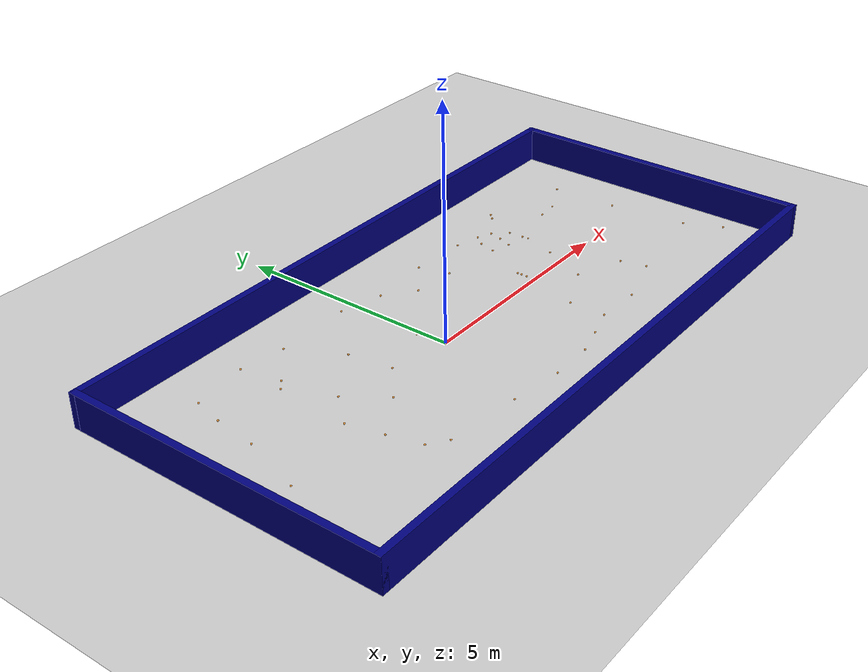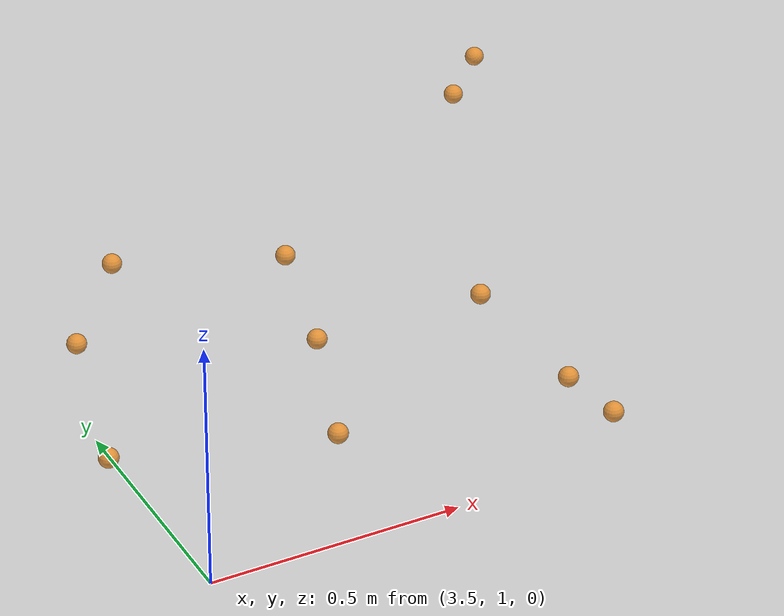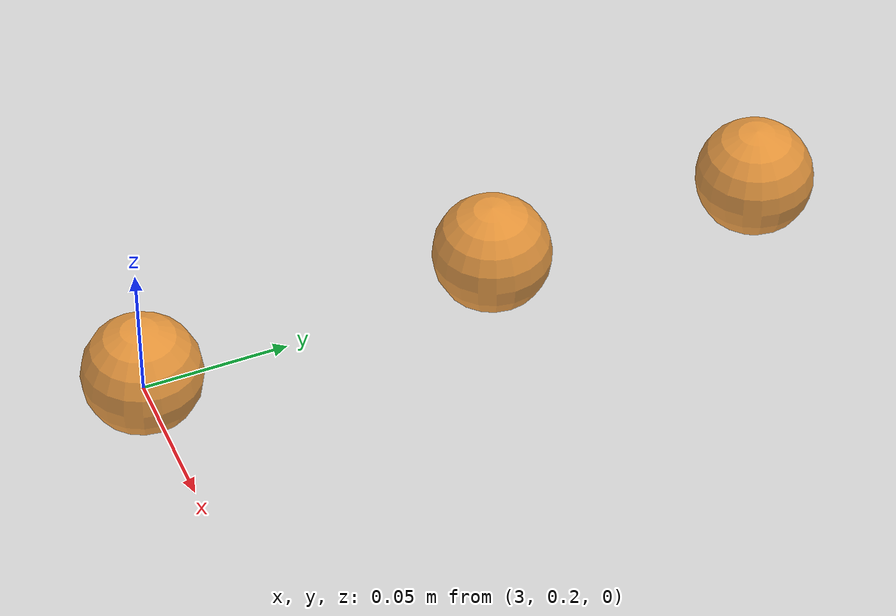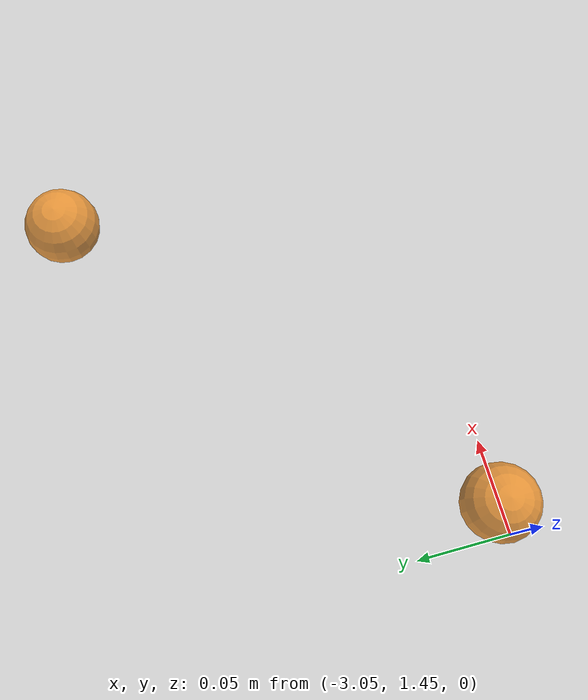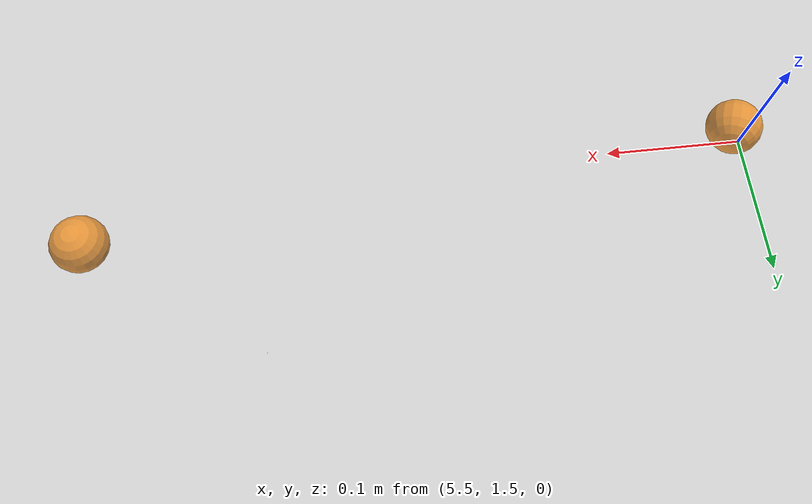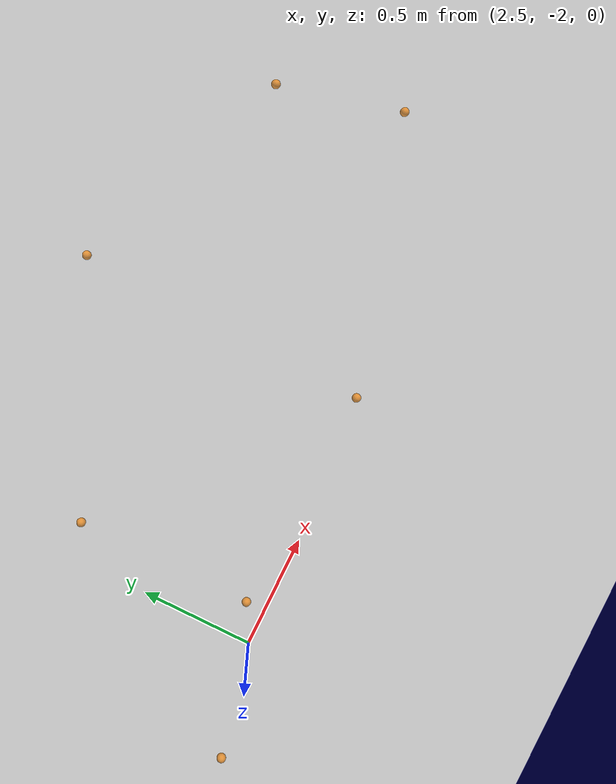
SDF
<sdf version="1.6">
 <world name="default">
  <model name="ground_plane">
   <static>1</static>
   <link name="link">
    <collision name="collision">
     <geometry><plane><normal>0 0 1</normal><size>100 100</size></plane></geometry>
     <surface><friction><ode><mu>100</mu><mu2>10</mu2></ode></friction></surface>
    </collision>
    <visual name="visual">
     <cast_shadows>0</cast_shadows>
     <geometry><plane><normal>0 0 1</normal><size>100 100</size></plane></geometry>
     <material>
      <script><uri>file://media/materials/scripts/gazebo.material</uri><name>Gazebo/Grey</name></script>
     </material>
    </visual>
   </link>
  </model>
  <gravity>0 0 -9.8</gravity>
  <magnetic_field>6e-06 2.3e-05 -4.2e-05</magnetic_field>
  <atmosphere type="adiabatic"/>
  <physics name="default_physics" default="0" type="ode">
   <max_step_size>0.001</max_step_size>
   <real_time_factor>1</real_time_factor>
   <real_time_update_rate>1000</real_time_update_rate>
  </physics>
  <scene><ambient>0.4 0.4 0.4 1</ambient><background>0.7 0.7 0.7 1</background><shadows>1</shadows></scene>
  <spherical_coordinates>
   <surface_model>EARTH_WGS84</surface_model>
   <latitude_deg>0</latitude_deg>
   <longitude_deg>0</longitude_deg>
   <elevation>0</elevation>
   <heading_deg>0</heading_deg>
  </spherical_coordinates>
  <model name="table_tennis_room_2">
   <pose>0.979802 0.03249 0 0 -0 0</pose>
   <link name="Wall_3">
    <collision name="Wall_3_Collision">
     <geometry><box><size>14 0.15 0.76</size></box></geometry>
     <pose>0 0 0.38 0 -0 0</pose>
    </collision>
    <visual name="Wall_3_Visual">
     <pose>0 0 0.38 0 -0 0</pose>
     <geometry><box><size>14 0.15 0.76</size></box></geometry>
     <material>
      <script><uri>file://media/materials/scripts/gazebo.material</uri><name>Gazebo/Grey</name></script>
      <ambient>0 0 0.498039 1</ambient>
     </material>
    </visual>
    <pose>0 -3.425 0 0 -0 0</pose>
   </link>
   <link name="Wall_4">
    <collision name="Wall_4_Collision">
     <geometry><box><size>7 0.15 0.76</size></box></geometry>
     <pose>0 0 0.38 0 -0 0</pose>
    </collision>
    <visual name="Wall_4_Visual">
     <pose>0 0 0.38 0 -0 0</pose>
     <geometry><box><size>7 0.15 0.76</size></box></geometry>
     <material>
      <script><uri>file://media/materials/scripts/gazebo.material</uri><name>Gazebo/Grey</name></script>
      <ambient>0 0 0.498039 1</ambient>
     </material>
    </visual>
    <pose>6.925 0 0 0 -0 1.5708</pose>
   </link>
   <link name="Wall_5">
    <collision name="Wall_5_Collision">
     <geometry><box><size>14 0.15 0.76</size></box></geometry>
     <pose>0 0 0.38 0 -0 0</pose>
    </collision>
    <visual name="Wall_5_Visual">
     <pose>0 0 0.38 0 -0 0</pose>
     <geometry><box><size>14 0.15 0.76</size></box></geometry>
     <material>
      <script><uri>file://media/materials/scripts/gazebo.material</uri><name>Gazebo/Grey</name></script>
      <ambient>0 0 0.498039 1</ambient>
     </material>
    </visual>
    <pose>0 3.425 0 0 -0 3.14159</pose>
   </link>
   <link name="Wall_6">
    <collision name="Wall_6_Collision">
     <geometry><box><size>7 0.15 0.76</size></box></geometry>
     <pose>0 0 0.38 0 -0 0</pose>
    </collision>
    <visual name="Wall_6_Visual">
     <pose>0 0 0.38 0 -0 0</pose>
     <geometry><box><size>7 0.15 0.76</size></box></geometry>
     <material>
      <script><uri>file://media/materials/scripts/gazebo.material</uri><name>Gazebo/Grey</name></script>
      <ambient>0 0 0.498039 1</ambient>
     </material>
    </visual>
    <pose>-6.925 0 0 0 0 -1.5708</pose>
   </link>
   <static>1</static>
  </model>
  <light name="main_light" type="directional">
   <pose>2.51103 2.03204 1 0 -0 0</pose>
   <diffuse>0.5 0.5 0.5 1</diffuse>
   <specular>0.1 0.1 0.1 1</specular>
   <direction>0.1 0.1 -0.9</direction>
   <attenuation>
    <range>20</range>
    <constant>0.5</constant>
    <linear>0.01</linear>
    <quadratic>0.001</quadratic>
   </attenuation>
  </light>
  <light name="sidelight_1" type="directional">
   <pose>2.54945 1.74337 1 0 -0 0</pose>
   <diffuse>0.5 0.5 0.5 1</diffuse>
   <specular>0.1 0.1 0.1 1</specular>
   <direction>0.1 0.1 -0.9</direction>
   <attenuation>
    <range>20</range>
    <constant>0.5</constant>
    <linear>0.01</linear>
    <quadratic>0.001</quadratic>
   </attenuation>
  </light>
  <light name="sidelight_2" type="directional">
   <pose>2.76871 0.675081 1 0 -0 0</pose>
   <diffuse>0.5 0.5 0.5 1</diffuse>
   <specular>0.1 0.1 0.1 1</specular>
   <direction>0.1 0.1 -0.9</direction>
   <attenuation>
    <range>20</range>
    <constant>0.5</constant>
    <linear>0.01</linear>
    <quadratic>0.001</quadratic>
   </attenuation>
  </light>
  <light name="sidelight_3" type="directional">
   <pose>2.93471 1.34637 1 0 -0 0</pose>
   <diffuse>0.5 0.5 0.5 1</diffuse>
   <specular>0.1 0.1 0.1 1</specular>
   <direction>0.1 0.1 -0.9</direction>
   <attenuation>
    <range>20</range>
    <constant>0.5</constant>
    <linear>0.01</linear>
    <quadratic>0.001</quadratic>
   </attenuation>
  </light>
  <light name="sidelight_4" type="directional">
   <pose>3.40089 1.34551 1 0 -0 0</pose>
   <diffuse>0.5 0.5 0.5 1</diffuse>
   <specular>0.1 0.1 0.1 1</specular>
   <direction>0.1 0.1 -0.9</direction>
   <attenuation>
    <range>20</range>
    <constant>0.5</constant>
    <linear>0.01</linear>
    <quadratic>0.001</quadratic>
   </attenuation>
  </light>
  <model name="table_tennis_24">
   <link name="link">
    <pose>0 0 0.02 0 -0 0</pose>
    <inertial>
     <mass>0.0027</mass>
     <inertia><ixx>0.00027</ixx><ixy>0</ixy><ixz>0</ixz><iyy>0.00027</iyy><iyz>0</iyz><izz>0.00027</izz></inertia>
    </inertial>
    <visual name="visual">
     <geometry><sphere><radius>0.02</radius></sphere></geometry>
     <material>
      <script><name>Gazebo/Orange</name><uri>file://media/materials/scripts/gazebo.material</uri></script>
      <ambient>1 0.44 0 1</ambient>
      <diffuse>1 0.44 0 1</diffuse>
      <specular>0 0 0 1</specular>
      <emissive>0 0 0 1</emissive>
      <shader type="vertex"><normal_map>__default__</normal_map></shader>
     </material>
     <cast_shadows>0</cast_shadows>
     <transparency>0.22</transparency>
    </visual>
    <collision name="collision">
     <geometry><sphere><radius>0.02</radius></sphere></geometry>
     <surface>
      <friction>
       <ode><mu>1</mu><mu2>1</mu2><fdir1>0 0 0</fdir1><slip1>0</slip1><slip2>0</slip2></ode>
       <torsional>
        <coefficient>1</coefficient>
        <patch_radius>0</patch_radius>
        <surface_radius>0</surface_radius>
        <use_patch_radius>1</use_patch_radius>
        <ode><slip>0</slip></ode>
       </torsional>
      </friction>
      <bounce><restitution_coefficient>0</restitution_coefficient><threshold>1e+06</threshold></bounce>
      <contact>
       <collide_without_contact>0</collide_without_contact>
       <collide_without_contact_bitmask>1</collide_without_contact_bitmask>
       <collide_bitmask>1</collide_bitmask>
       <ode>
        <soft_cfm>0</soft_cfm>
        <soft_erp>0.2</soft_erp>
        <kp>1e+13</kp>
        <kd>1</kd>
        <max_vel>0.01</max_vel>
        <min_depth>0</min_depth>
       </ode>
       <bullet>
        <split_impulse>1</split_impulse>
        <split_impulse_penetration_threshold>-0.01</split_impulse_penetration_threshold>
        <soft_cfm>0</soft_cfm>
        <soft_erp>0.2</soft_erp>
        <kp>1e+13</kp>
        <kd>1</kd>
       </bullet>
      </contact>
     </surface>
    </collision>
   </link>
   <static>0</static>
   <pose>4.39239 1.11321 0 0 -0 0</pose>
  </model>
  <model name="table_tennis_25">
   <link name="link">
    <pose>0 0 0.02 0 -0 0</pose>
    <inertial>
     <mass>0.0027</mass>
     <inertia><ixx>0.00027</ixx><ixy>0</ixy><ixz>0</ixz><iyy>0.00027</iyy><iyz>0</iyz><izz>0.00027</izz></inertia>
    </inertial>
    <visual name="visual">
     <geometry><sphere><radius>0.02</radius></sphere></geometry>
     <material>
      <script><name>Gazebo/Orange</name><uri>file://media/materials/scripts/gazebo.material</uri></script>
      <ambient>1 0.44 0 1</ambient>
      <diffuse>1 0.44 0 1</diffuse>
      <specular>0 0 0 1</specular>
      <emissive>0 0 0 1</emissive>
      <shader type="vertex"><normal_map>__default__</normal_map></shader>
     </material>
     <cast_shadows>0</cast_shadows>
     <transparency>0.22</transparency>
    </visual>
    <collision name="collision">
     <geometry><sphere><radius>0.02</radius></sphere></geometry>
     <surface>
      <friction>
       <ode><mu>1</mu><mu2>1</mu2><fdir1>0 0 0</fdir1><slip1>0</slip1><slip2>0</slip2></ode>
       <torsional>
        <coefficient>1</coefficient>
        <patch_radius>0</patch_radius>
        <surface_radius>0</surface_radius>
        <use_patch_radius>1</use_patch_radius>
        <ode><slip>0</slip></ode>
       </torsional>
      </friction>
      <bounce><restitution_coefficient>0</restitution_coefficient><threshold>1e+06</threshold></bounce>
      <contact>
       <collide_without_contact>0</collide_without_contact>
       <collide_without_contact_bitmask>1</collide_without_contact_bitmask>
       <collide_bitmask>1</collide_bitmask>
       <ode>
        <soft_cfm>0</soft_cfm>
        <soft_erp>0.2</soft_erp>
        <kp>1e+13</kp>
        <kd>1</kd>
        <max_vel>0.01</max_vel>
        <min_depth>0</min_depth>
       </ode>
       <bullet>
        <split_impulse>1</split_impulse>
        <split_impulse_penetration_threshold>-0.01</split_impulse_penetration_threshold>
        <soft_cfm>0</soft_cfm>
        <soft_erp>0.2</soft_erp>
        <kp>1e+13</kp>
        <kd>1</kd>
       </bullet>
      </contact>
     </surface>
    </collision>
   </link>
   <static>0</static>
   <pose>4.73636 -1.05166 0.010875 1.01076 0.53772 3.12203</pose>
  </model>
  <model name="table_tennis_26">
   <link name="link">
    <pose>0 0 0.02 0 -0 0</pose>
    <inertial>
     <mass>0.0027</mass>
     <inertia><ixx>0.00027</ixx><ixy>0</ixy><ixz>0</ixz><iyy>0.00027</iyy><iyz>0</iyz><izz>0.00027</izz></inertia>
    </inertial>
    <visual name="visual">
     <geometry><sphere><radius>0.02</radius></sphere></geometry>
     <material>
      <script><name>Gazebo/Orange</name><uri>file://media/materials/scripts/gazebo.material</uri></script>
      <ambient>1 0.44 0 1</ambient>
      <diffuse>1 0.44 0 1</diffuse>
      <specular>0 0 0 1</specular>
      <emissive>0 0 0 1</emissive>
      <shader type="vertex"><normal_map>__default__</normal_map></shader>
     </material>
     <cast_shadows>0</cast_shadows>
     <transparency>0.22</transparency>
    </visual>
    <collision name="collision">
     <geometry><sphere><radius>0.02</radius></sphere></geometry>
     <surface>
      <friction>
       <ode><mu>1</mu><mu2>1</mu2><fdir1>0 0 0</fdir1><slip1>0</slip1><slip2>0</slip2></ode>
       <torsional>
        <coefficient>1</coefficient>
        <patch_radius>0</patch_radius>
        <surface_radius>0</surface_radius>
        <use_patch_radius>1</use_patch_radius>
        <ode><slip>0</slip></ode>
       </torsional>
      </friction>
      <bounce><restitution_coefficient>0</restitution_coefficient><threshold>1e+06</threshold></bounce>
      <contact>
       <collide_without_contact>0</collide_without_contact>
       <collide_without_contact_bitmask>1</collide_without_contact_bitmask>
       <collide_bitmask>1</collide_bitmask>
       <ode>
        <soft_cfm>0</soft_cfm>
        <soft_erp>0.2</soft_erp>
        <kp>1e+13</kp>
        <kd>1</kd>
        <max_vel>0.01</max_vel>
        <min_depth>0</min_depth>
       </ode>
       <bullet>
        <split_impulse>1</split_impulse>
        <split_impulse_penetration_threshold>-0.01</split_impulse_penetration_threshold>
        <soft_cfm>0</soft_cfm>
        <soft_erp>0.2</soft_erp>
        <kp>1e+13</kp>
        <kd>1</kd>
       </bullet>
      </contact>
     </surface>
    </collision>
   </link>
   <static>0</static>
   <pose>4.14925 0.378006 0 0 -0 0</pose>
  </model>
  <model name="table_tennis_27">
   <link name="link">
    <pose>0 0 0.02 0 -0 0</pose>
    <inertial>
     <mass>0.0027</mass>
     <inertia><ixx>0.00027</ixx><ixy>0</ixy><ixz>0</ixz><iyy>0.00027</iyy><iyz>0</iyz><izz>0.00027</izz></inertia>
    </inertial>
    <visual name="visual">
     <geometry><sphere><radius>0.02</radius></sphere></geometry>
     <material>
      <script><name>Gazebo/Orange</name><uri>file://media/materials/scripts/gazebo.material</uri></script>
      <ambient>1 0.44 0 1</ambient>
      <diffuse>1 0.44 0 1</diffuse>
      <specular>0 0 0 1</specular>
      <emissive>0 0 0 1</emissive>
      <shader type="vertex"><normal_map>__default__</normal_map></shader>
     </material>
     <cast_shadows>0</cast_shadows>
     <transparency>0.22</transparency>
    </visual>
    <collision name="collision">
     <geometry><sphere><radius>0.02</radius></sphere></geometry>
     <surface>
      <friction>
       <ode><mu>1</mu><mu2>1</mu2><fdir1>0 0 0</fdir1><slip1>0</slip1><slip2>0</slip2></ode>
       <torsional>
        <coefficient>1</coefficient>
        <patch_radius>0</patch_radius>
        <surface_radius>0</surface_radius>
        <use_patch_radius>1</use_patch_radius>
        <ode><slip>0</slip></ode>
       </torsional>
      </friction>
      <bounce><restitution_coefficient>0</restitution_coefficient><threshold>1e+06</threshold></bounce>
      <contact>
       <collide_without_contact>0</collide_without_contact>
       <collide_without_contact_bitmask>1</collide_without_contact_bitmask>
       <collide_bitmask>1</collide_bitmask>
       <ode>
        <soft_cfm>0</soft_cfm>
        <soft_erp>0.2</soft_erp>
        <kp>1e+13</kp>
        <kd>1</kd>
        <max_vel>0.01</max_vel>
        <min_depth>0</min_depth>
       </ode>
       <bullet>
        <split_impulse>1</split_impulse>
        <split_impulse_penetration_threshold>-0.01</split_impulse_penetration_threshold>
        <soft_cfm>0</soft_cfm>
        <soft_erp>0.2</soft_erp>
        <kp>1e+13</kp>
        <kd>1</kd>
       </bullet>
      </contact>
     </surface>
    </collision>
   </link>
   <static>0</static>
   <pose>3.48735 1.41347 0 0 -0 0</pose>
  </model>
  <model name="table_tennis_28">
   <link name="link">
    <pose>0 0 0.02 0 -0 0</pose>
    <inertial>
     <mass>0.0027</mass>
     <inertia><ixx>0.00027</ixx><ixy>0</ixy><ixz>0</ixz><iyy>0.00027</iyy><iyz>0</iyz><izz>0.00027</izz></inertia>
    </inertial>
    <visual name="visual">
     <geometry><sphere><radius>0.02</radius></sphere></geometry>
     <material>
      <script><name>Gazebo/Orange</name><uri>file://media/materials/scripts/gazebo.material</uri></script>
      <ambient>1 0.44 0 1</ambient>
      <diffuse>1 0.44 0 1</diffuse>
      <specular>0 0 0 1</specular>
      <emissive>0 0 0 1</emissive>
      <shader type="vertex"><normal_map>__default__</normal_map></shader>
     </material>
     <cast_shadows>0</cast_shadows>
     <transparency>0.22</transparency>
    </visual>
    <collision name="collision">
     <geometry><sphere><radius>0.02</radius></sphere></geometry>
     <surface>
      <friction>
       <ode><mu>1</mu><mu2>1</mu2><fdir1>0 0 0</fdir1><slip1>0</slip1><slip2>0</slip2></ode>
       <torsional>
        <coefficient>1</coefficient>
        <patch_radius>0</patch_radius>
        <surface_radius>0</surface_radius>
        <use_patch_radius>1</use_patch_radius>
        <ode><slip>0</slip></ode>
       </torsional>
      </friction>
      <bounce><restitution_coefficient>0</restitution_coefficient><threshold>1e+06</threshold></bounce>
      <contact>
       <collide_without_contact>0</collide_without_contact>
       <collide_without_contact_bitmask>1</collide_without_contact_bitmask>
       <collide_bitmask>1</collide_bitmask>
       <ode>
        <soft_cfm>0</soft_cfm>
        <soft_erp>0.2</soft_erp>
        <kp>1e+13</kp>
        <kd>1</kd>
        <max_vel>0.01</max_vel>
        <min_depth>0</min_depth>
       </ode>
       <bullet>
        <split_impulse>1</split_impulse>
        <split_impulse_penetration_threshold>-0.01</split_impulse_penetration_threshold>
        <soft_cfm>0</soft_cfm>
        <soft_erp>0.2</soft_erp>
        <kp>1e+13</kp>
        <kd>1</kd>
       </bullet>
      </contact>
     </surface>
    </collision>
   </link>
   <static>0</static>
   <pose>5.98062 1.54014 4e-06 0.018571 -0.007017 -0.002142</pose>
  </model>
  <model name="table_tennis_29">
   <link name="link">
    <pose>0 0 0.02 0 -0 0</pose>
    <inertial>
     <mass>0.0027</mass>
     <inertia><ixx>0.00027</ixx><ixy>0</ixy><ixz>0</ixz><iyy>0.00027</iyy><iyz>0</iyz><izz>0.00027</izz></inertia>
    </inertial>
    <visual name="visual">
     <geometry><sphere><radius>0.02</radius></sphere></geometry>
     <material>
      <script><name>Gazebo/Orange</name><uri>file://media/materials/scripts/gazebo.material</uri></script>
      <ambient>1 0.44 0 1</ambient>
      <diffuse>1 0.44 0 1</diffuse>
      <specular>0 0 0 1</specular>
      <emissive>0 0 0 1</emissive>
      <shader type="vertex"><normal_map>__default__</normal_map></shader>
     </material>
     <cast_shadows>0</cast_shadows>
     <transparency>0.22</transparency>
    </visual>
    <collision name="collision">
     <geometry><sphere><radius>0.02</radius></sphere></geometry>
     <surface>
      <friction>
       <ode><mu>1</mu><mu2>1</mu2><fdir1>0 0 0</fdir1><slip1>0</slip1><slip2>0</slip2></ode>
       <torsional>
        <coefficient>1</coefficient>
        <patch_radius>0</patch_radius>
        <surface_radius>0</surface_radius>
        <use_patch_radius>1</use_patch_radius>
        <ode><slip>0</slip></ode>
       </torsional>
      </friction>
      <bounce><restitution_coefficient>0</restitution_coefficient><threshold>1e+06</threshold></bounce>
      <contact>
       <collide_without_contact>0</collide_without_contact>
       <collide_without_contact_bitmask>1</collide_without_contact_bitmask>
       <collide_bitmask>1</collide_bitmask>
       <ode>
        <soft_cfm>0</soft_cfm>
        <soft_erp>0.2</soft_erp>
        <kp>1e+13</kp>
        <kd>1</kd>
        <max_vel>0.01</max_vel>
        <min_depth>0</min_depth>
       </ode>
       <bullet>
        <split_impulse>1</split_impulse>
        <split_impulse_penetration_threshold>-0.01</split_impulse_penetration_threshold>
        <soft_cfm>0</soft_cfm>
        <soft_erp>0.2</soft_erp>
        <kp>1e+13</kp>
        <kd>1</kd>
       </bullet>
      </contact>
     </surface>
    </collision>
   </link>
   <static>0</static>
   <pose>5.501 1.47848 0.017454 -1.22525 -1.18556 -0.737554</pose>
  </model>
  <model name="table_tennis_30">
   <link name="link">
    <pose>0 0 0.02 0 -0 0</pose>
    <inertial>
     <mass>0.0027</mass>
     <inertia><ixx>0.00027</ixx><ixy>0</ixy><ixz>0</ixz><iyy>0.00027</iyy><iyz>0</iyz><izz>0.00027</izz></inertia>
    </inertial>
    <visual name="visual">
     <geometry><sphere><radius>0.02</radius></sphere></geometry>
     <material>
      <script><name>Gazebo/Orange</name><uri>file://media/materials/scripts/gazebo.material</uri></script>
      <ambient>1 0.44 0 1</ambient>
      <diffuse>1 0.44 0 1</diffuse>
      <specular>0 0 0 1</specular>
      <emissive>0 0 0 1</emissive>
      <shader type="vertex"><normal_map>__default__</normal_map></shader>
     </material>
     <cast_shadows>0</cast_shadows>
     <transparency>0.22</transparency>
    </visual>
    <collision name="collision">
     <geometry><sphere><radius>0.02</radius></sphere></geometry>
     <surface>
      <friction>
       <ode><mu>1</mu><mu2>1</mu2><fdir1>0 0 0</fdir1><slip1>0</slip1><slip2>0</slip2></ode>
       <torsional>
        <coefficient>1</coefficient>
        <patch_radius>0</patch_radius>
        <surface_radius>0</surface_radius>
        <use_patch_radius>1</use_patch_radius>
        <ode><slip>0</slip></ode>
       </torsional>
      </friction>
      <bounce><restitution_coefficient>0</restitution_coefficient><threshold>1e+06</threshold></bounce>
      <contact>
       <collide_without_contact>0</collide_without_contact>
       <collide_without_contact_bitmask>1</collide_without_contact_bitmask>
       <collide_bitmask>1</collide_bitmask>
       <ode>
        <soft_cfm>0</soft_cfm>
        <soft_erp>0.2</soft_erp>
        <kp>1e+13</kp>
        <kd>1</kd>
        <max_vel>0.01</max_vel>
        <min_depth>0</min_depth>
       </ode>
       <bullet>
        <split_impulse>1</split_impulse>
        <split_impulse_penetration_threshold>-0.01</split_impulse_penetration_threshold>
        <soft_cfm>0</soft_cfm>
        <soft_erp>0.2</soft_erp>
        <kp>1e+13</kp>
        <kd>1</kd>
       </bullet>
      </contact>
     </surface>
    </collision>
   </link>
   <static>0</static>
   <pose>3.7053 -0.627186 0 0 -0 0</pose>
  </model>
  <model name="table_tennis_31">
   <link name="link">
    <pose>0 0 0.02 0 -0 0</pose>
    <inertial>
     <mass>0.0027</mass>
     <inertia><ixx>0.00027</ixx><ixy>0</ixy><ixz>0</ixz><iyy>0.00027</iyy><iyz>0</iyz><izz>0.00027</izz></inertia>
    </inertial>
    <visual name="visual">
     <geometry><sphere><radius>0.02</radius></sphere></geometry>
     <material>
      <script><name>Gazebo/Orange</name><uri>file://media/materials/scripts/gazebo.material</uri></script>
      <ambient>1 0.44 0 1</ambient>
      <diffuse>1 0.44 0 1</diffuse>
      <specular>0 0 0 1</specular>
      <emissive>0 0 0 1</emissive>
      <shader type="vertex"><normal_map>__default__</normal_map></shader>
     </material>
     <cast_shadows>0</cast_shadows>
     <transparency>0.22</transparency>
    </visual>
    <collision name="collision">
     <geometry><sphere><radius>0.02</radius></sphere></geometry>
     <surface>
      <friction>
       <ode><mu>1</mu><mu2>1</mu2><fdir1>0 0 0</fdir1><slip1>0</slip1><slip2>0</slip2></ode>
       <torsional>
        <coefficient>1</coefficient>
        <patch_radius>0</patch_radius>
        <surface_radius>0</surface_radius>
        <use_patch_radius>1</use_patch_radius>
        <ode><slip>0</slip></ode>
       </torsional>
      </friction>
      <bounce><restitution_coefficient>0</restitution_coefficient><threshold>1e+06</threshold></bounce>
      <contact>
       <collide_without_contact>0</collide_without_contact>
       <collide_without_contact_bitmask>1</collide_without_contact_bitmask>
       <collide_bitmask>1</collide_bitmask>
       <ode>
        <soft_cfm>0</soft_cfm>
        <soft_erp>0.2</soft_erp>
        <kp>1e+13</kp>
        <kd>1</kd>
        <max_vel>0.01</max_vel>
        <min_depth>0</min_depth>
       </ode>
       <bullet>
        <split_impulse>1</split_impulse>
        <split_impulse_penetration_threshold>-0.01</split_impulse_penetration_threshold>
        <soft_cfm>0</soft_cfm>
        <soft_erp>0.2</soft_erp>
        <kp>1e+13</kp>
        <kd>1</kd>
       </bullet>
      </contact>
     </surface>
    </collision>
   </link>
   <static>0</static>
   <pose>2.65661 -1.11662 0 0 -0 0</pose>
  </model>
  <model name="table_tennis_32">
   <link name="link">
    <pose>0 0 0.02 0 -0 0</pose>
    <inertial>
     <mass>0.0027</mass>
     <inertia><ixx>0.00027</ixx><ixy>0</ixy><ixz>0</ixz><iyy>0.00027</iyy><iyz>0</iyz><izz>0.00027</izz></inertia>
    </inertial>
    <visual name="visual">
     <geometry><sphere><radius>0.02</radius></sphere></geometry>
     <material>
      <script><name>Gazebo/Orange</name><uri>file://media/materials/scripts/gazebo.material</uri></script>
      <ambient>1 0.44 0 1</ambient>
      <diffuse>1 0.44 0 1</diffuse>
      <specular>0 0 0 1</specular>
      <emissive>0 0 0 1</emissive>
      <shader type="vertex"><normal_map>__default__</normal_map></shader>
     </material>
     <cast_shadows>0</cast_shadows>
     <transparency>0.22</transparency>
    </visual>
    <collision name="collision">
     <geometry><sphere><radius>0.02</radius></sphere></geometry>
     <surface>
      <friction>
       <ode><mu>1</mu><mu2>1</mu2><fdir1>0 0 0</fdir1><slip1>0</slip1><slip2>0</slip2></ode>
       <torsional>
        <coefficient>1</coefficient>
        <patch_radius>0</patch_radius>
        <surface_radius>0</surface_radius>
        <use_patch_radius>1</use_patch_radius>
        <ode><slip>0</slip></ode>
       </torsional>
      </friction>
      <bounce><restitution_coefficient>0</restitution_coefficient><threshold>1e+06</threshold></bounce>
      <contact>
       <collide_without_contact>0</collide_without_contact>
       <collide_without_contact_bitmask>1</collide_without_contact_bitmask>
       <collide_bitmask>1</collide_bitmask>
       <ode>
        <soft_cfm>0</soft_cfm>
        <soft_erp>0.2</soft_erp>
        <kp>1e+13</kp>
        <kd>1</kd>
        <max_vel>0.01</max_vel>
        <min_depth>0</min_depth>
       </ode>
       <bullet>
        <split_impulse>1</split_impulse>
        <split_impulse_penetration_threshold>-0.01</split_impulse_penetration_threshold>
        <soft_cfm>0</soft_cfm>
        <soft_erp>0.2</soft_erp>
        <kp>1e+13</kp>
        <kd>1</kd>
       </bullet>
      </contact>
     </surface>
    </collision>
   </link>
   <static>0</static>
   <pose>4.86946 -1.58779 0 0 -0 0</pose>
  </model>
  <model name="table_tennis_33">
   <link name="link">
    <pose>0 0 0.02 0 -0 0</pose>
    <inertial>
     <mass>0.0027</mass>
     <inertia><ixx>0.00027</ixx><ixy>0</ixy><ixz>0</ixz><iyy>0.00027</iyy><iyz>0</iyz><izz>0.00027</izz></inertia>
    </inertial>
    <visual name="visual">
     <geometry><sphere><radius>0.02</radius></sphere></geometry>
     <material>
      <script><name>Gazebo/Orange</name><uri>file://media/materials/scripts/gazebo.material</uri></script>
      <ambient>1 0.44 0 1</ambient>
      <diffuse>1 0.44 0 1</diffuse>
      <specular>0 0 0 1</specular>
      <emissive>0 0 0 1</emissive>
      <shader type="vertex"><normal_map>__default__</normal_map></shader>
     </material>
     <cast_shadows>0</cast_shadows>
     <transparency>0.22</transparency>
    </visual>
    <collision name="collision">
     <geometry><sphere><radius>0.02</radius></sphere></geometry>
     <surface>
      <friction>
       <ode><mu>1</mu><mu2>1</mu2><fdir1>0 0 0</fdir1><slip1>0</slip1><slip2>0</slip2></ode>
       <torsional>
        <coefficient>1</coefficient>
        <patch_radius>0</patch_radius>
        <surface_radius>0</surface_radius>
        <use_patch_radius>1</use_patch_radius>
        <ode><slip>0</slip></ode>
       </torsional>
      </friction>
      <bounce><restitution_coefficient>0</restitution_coefficient><threshold>1e+06</threshold></bounce>
      <contact>
       <collide_without_contact>0</collide_without_contact>
       <collide_without_contact_bitmask>1</collide_without_contact_bitmask>
       <collide_bitmask>1</collide_bitmask>
       <ode>
        <soft_cfm>0</soft_cfm>
        <soft_erp>0.2</soft_erp>
        <kp>1e+13</kp>
        <kd>1</kd>
        <max_vel>0.01</max_vel>
        <min_depth>0</min_depth>
       </ode>
       <bullet>
        <split_impulse>1</split_impulse>
        <split_impulse_penetration_threshold>-0.01</split_impulse_penetration_threshold>
        <soft_cfm>0</soft_cfm>
        <soft_erp>0.2</soft_erp>
        <kp>1e+13</kp>
        <kd>1</kd>
       </bullet>
      </contact>
     </surface>
    </collision>
   </link>
   <static>0</static>
   <pose>5.98906 -3.28803 0.023626 1.83335 -0.797566 0.878143</pose>
  </model>
  <model name="table_tennis_34">
   <link name="link">
    <pose>0 0 0.02 0 -0 0</pose>
    <inertial>
     <mass>0.0027</mass>
     <inertia><ixx>0.00027</ixx><ixy>0</ixy><ixz>0</ixz><iyy>0.00027</iyy><iyz>0</iyz><izz>0.00027</izz></inertia>
    </inertial>
    <visual name="visual">
     <geometry><sphere><radius>0.02</radius></sphere></geometry>
     <material>
      <script><name>Gazebo/Orange</name><uri>file://media/materials/scripts/gazebo.material</uri></script>
      <ambient>1 0.44 0 1</ambient>
      <diffuse>1 0.44 0 1</diffuse>
      <specular>0 0 0 1</specular>
      <emissive>0 0 0 1</emissive>
      <shader type="vertex"><normal_map>__default__</normal_map></shader>
     </material>
     <cast_shadows>0</cast_shadows>
     <transparency>0.22</transparency>
    </visual>
    <collision name="collision">
     <geometry><sphere><radius>0.02</radius></sphere></geometry>
     <surface>
      <friction>
       <ode><mu>1</mu><mu2>1</mu2><fdir1>0 0 0</fdir1><slip1>0</slip1><slip2>0</slip2></ode>
       <torsional>
        <coefficient>1</coefficient>
        <patch_radius>0</patch_radius>
        <surface_radius>0</surface_radius>
        <use_patch_radius>1</use_patch_radius>
        <ode><slip>0</slip></ode>
       </torsional>
      </friction>
      <bounce><restitution_coefficient>0</restitution_coefficient><threshold>1e+06</threshold></bounce>
      <contact>
       <collide_without_contact>0</collide_without_contact>
       <collide_without_contact_bitmask>1</collide_without_contact_bitmask>
       <collide_bitmask>1</collide_bitmask>
       <ode>
        <soft_cfm>0</soft_cfm>
        <soft_erp>0.2</soft_erp>
        <kp>1e+13</kp>
        <kd>1</kd>
        <max_vel>0.01</max_vel>
        <min_depth>0</min_depth>
       </ode>
       <bullet>
        <split_impulse>1</split_impulse>
        <split_impulse_penetration_threshold>-0.01</split_impulse_penetration_threshold>
        <soft_cfm>0</soft_cfm>
        <soft_erp>0.2</soft_erp>
        <kp>1e+13</kp>
        <kd>1</kd>
       </bullet>
      </contact>
     </surface>
    </collision>
   </link>
   <static>0</static>
   <pose>4.79441 2.4169 0.035111 -2.68476 -0.570081 -0.103876</pose>
  </model>
  <model name="table_tennis_35">
   <link name="link">
    <pose>0 0 0.02 0 -0 0</pose>
    <inertial>
     <mass>0.0027</mass>
     <inertia><ixx>0.00027</ixx><ixy>0</ixy><ixz>0</ixz><iyy>0.00027</iyy><iyz>0</iyz><izz>0.00027</izz></inertia>
    </inertial>
    <visual name="visual">
     <geometry><sphere><radius>0.02</radius></sphere></geometry>
     <material>
      <script><name>Gazebo/Orange</name><uri>file://media/materials/scripts/gazebo.material</uri></script>
      <ambient>1 0.44 0 1</ambient>
      <diffuse>1 0.44 0 1</diffuse>
      <specular>0 0 0 1</specular>
      <emissive>0 0 0 1</emissive>
      <shader type="vertex"><normal_map>__default__</normal_map></shader>
     </material>
     <cast_shadows>0</cast_shadows>
     <transparency>0.22</transparency>
    </visual>
    <collision name="collision">
     <geometry><sphere><radius>0.02</radius></sphere></geometry>
     <surface>
      <friction>
       <ode><mu>1</mu><mu2>1</mu2><fdir1>0 0 0</fdir1><slip1>0</slip1><slip2>0</slip2></ode>
       <torsional>
        <coefficient>1</coefficient>
        <patch_radius>0</patch_radius>
        <surface_radius>0</surface_radius>
        <use_patch_radius>1</use_patch_radius>
        <ode><slip>0</slip></ode>
       </torsional>
      </friction>
      <bounce><restitution_coefficient>0</restitution_coefficient><threshold>1e+06</threshold></bounce>
      <contact>
       <collide_without_contact>0</collide_without_contact>
       <collide_without_contact_bitmask>1</collide_without_contact_bitmask>
       <collide_bitmask>1</collide_bitmask>
       <ode>
        <soft_cfm>0</soft_cfm>
        <soft_erp>0.2</soft_erp>
        <kp>1e+13</kp>
        <kd>1</kd>
        <max_vel>0.01</max_vel>
        <min_depth>0</min_depth>
       </ode>
       <bullet>
        <split_impulse>1</split_impulse>
        <split_impulse_penetration_threshold>-0.01</split_impulse_penetration_threshold>
        <soft_cfm>0</soft_cfm>
        <soft_erp>0.2</soft_erp>
        <kp>1e+13</kp>
        <kd>1</kd>
       </bullet>
      </contact>
     </surface>
    </collision>
   </link>
   <static>0</static>
   <pose>-0.108036 0.630376 0 0 -0 0</pose>
  </model>
  <model name="table_tennis_36">
   <link name="link">
    <pose>0 0 0.02 0 -0 0</pose>
    <inertial>
     <mass>0.0027</mass>
     <inertia><ixx>0.00027</ixx><ixy>0</ixy><ixz>0</ixz><iyy>0.00027</iyy><iyz>0</iyz><izz>0.00027</izz></inertia>
    </inertial>
    <visual name="visual">
     <geometry><sphere><radius>0.02</radius></sphere></geometry>
     <material>
      <script><name>Gazebo/Orange</name><uri>file://media/materials/scripts/gazebo.material</uri></script>
      <ambient>1 0.44 0 1</ambient>
      <diffuse>1 0.44 0 1</diffuse>
      <specular>0 0 0 1</specular>
      <emissive>0 0 0 1</emissive>
      <shader type="vertex"><normal_map>__default__</normal_map></shader>
     </material>
     <cast_shadows>0</cast_shadows>
     <transparency>0.22</transparency>
    </visual>
    <collision name="collision">
     <geometry><sphere><radius>0.02</radius></sphere></geometry>
     <surface>
      <friction>
       <ode><mu>1</mu><mu2>1</mu2><fdir1>0 0 0</fdir1><slip1>0</slip1><slip2>0</slip2></ode>
       <torsional>
        <coefficient>1</coefficient>
        <patch_radius>0</patch_radius>
        <surface_radius>0</surface_radius>
        <use_patch_radius>1</use_patch_radius>
        <ode><slip>0</slip></ode>
       </torsional>
      </friction>
      <bounce><restitution_coefficient>0</restitution_coefficient><threshold>1e+06</threshold></bounce>
      <contact>
       <collide_without_contact>0</collide_without_contact>
       <collide_without_contact_bitmask>1</collide_without_contact_bitmask>
       <collide_bitmask>1</collide_bitmask>
       <ode>
        <soft_cfm>0</soft_cfm>
        <soft_erp>0.2</soft_erp>
        <kp>1e+13</kp>
        <kd>1</kd>
        <max_vel>0.01</max_vel>
        <min_depth>0</min_depth>
       </ode>
       <bullet>
        <split_impulse>1</split_impulse>
        <split_impulse_penetration_threshold>-0.01</split_impulse_penetration_threshold>
        <soft_cfm>0</soft_cfm>
        <soft_erp>0.2</soft_erp>
        <kp>1e+13</kp>
        <kd>1</kd>
       </bullet>
      </contact>
     </surface>
    </collision>
   </link>
   <static>0</static>
   <pose>-1.43818 1.21902 0 0 -0 0</pose>
  </model>
  <model name="table_tennis_37">
   <link name="link">
    <pose>0 0 0.02 0 -0 0</pose>
    <inertial>
     <mass>0.0027</mass>
     <inertia><ixx>0.00027</ixx><ixy>0</ixy><ixz>0</ixz><iyy>0.00027</iyy><iyz>0</iyz><izz>0.00027</izz></inertia>
    </inertial>
    <visual name="visual">
     <geometry><sphere><radius>0.02</radius></sphere></geometry>
     <material>
      <script><name>Gazebo/Orange</name><uri>file://media/materials/scripts/gazebo.material</uri></script>
      <ambient>1 0.44 0 1</ambient>
      <diffuse>1 0.44 0 1</diffuse>
      <specular>0 0 0 1</specular>
      <emissive>0 0 0 1</emissive>
      <shader type="vertex"><normal_map>__default__</normal_map></shader>
     </material>
     <cast_shadows>0</cast_shadows>
     <transparency>0.22</transparency>
    </visual>
    <collision name="collision">
     <geometry><sphere><radius>0.02</radius></sphere></geometry>
     <surface>
      <friction>
       <ode><mu>1</mu><mu2>1</mu2><fdir1>0 0 0</fdir1><slip1>0</slip1><slip2>0</slip2></ode>
       <torsional>
        <coefficient>1</coefficient>
        <patch_radius>0</patch_radius>
        <surface_radius>0</surface_radius>
        <use_patch_radius>1</use_patch_radius>
        <ode><slip>0</slip></ode>
       </torsional>
      </friction>
      <bounce><restitution_coefficient>0</restitution_coefficient><threshold>1e+06</threshold></bounce>
      <contact>
       <collide_without_contact>0</collide_without_contact>
       <collide_without_contact_bitmask>1</collide_without_contact_bitmask>
       <collide_bitmask>1</collide_bitmask>
       <ode>
        <soft_cfm>0</soft_cfm>
        <soft_erp>0.2</soft_erp>
        <kp>1e+13</kp>
        <kd>1</kd>
        <max_vel>0.01</max_vel>
        <min_depth>0</min_depth>
       </ode>
       <bullet>
        <split_impulse>1</split_impulse>
        <split_impulse_penetration_threshold>-0.01</split_impulse_penetration_threshold>
        <soft_cfm>0</soft_cfm>
        <soft_erp>0.2</soft_erp>
        <kp>1e+13</kp>
        <kd>1</kd>
       </bullet>
      </contact>
     </surface>
    </collision>
   </link>
   <static>0</static>
   <pose>1.95632 2.22393 0 0 -0 0</pose>
  </model>
  <model name="table_tennis_38">
   <link name="link">
    <pose>0 0 0.02 0 -0 0</pose>
    <inertial>
     <mass>0.0027</mass>
     <inertia><ixx>0.00027</ixx><ixy>0</ixy><ixz>0</ixz><iyy>0.00027</iyy><iyz>0</iyz><izz>0.00027</izz></inertia>
    </inertial>
    <visual name="visual">
     <geometry><sphere><radius>0.02</radius></sphere></geometry>
     <material>
      <script><name>Gazebo/Orange</name><uri>file://media/materials/scripts/gazebo.material</uri></script>
      <ambient>1 0.44 0 1</ambient>
      <diffuse>1 0.44 0 1</diffuse>
      <specular>0 0 0 1</specular>
      <emissive>0 0 0 1</emissive>
      <shader type="vertex"><normal_map>__default__</normal_map></shader>
     </material>
     <cast_shadows>0</cast_shadows>
     <transparency>0.22</transparency>
    </visual>
    <collision name="collision">
     <geometry><sphere><radius>0.02</radius></sphere></geometry>
     <surface>
      <friction>
       <ode><mu>1</mu><mu2>1</mu2><fdir1>0 0 0</fdir1><slip1>0</slip1><slip2>0</slip2></ode>
       <torsional>
        <coefficient>1</coefficient>
        <patch_radius>0</patch_radius>
        <surface_radius>0</surface_radius>
        <use_patch_radius>1</use_patch_radius>
        <ode><slip>0</slip></ode>
       </torsional>
      </friction>
      <bounce><restitution_coefficient>0</restitution_coefficient><threshold>1e+06</threshold></bounce>
      <contact>
       <collide_without_contact>0</collide_without_contact>
       <collide_without_contact_bitmask>1</collide_without_contact_bitmask>
       <collide_bitmask>1</collide_bitmask>
       <ode>
        <soft_cfm>0</soft_cfm>
        <soft_erp>0.2</soft_erp>
        <kp>1e+13</kp>
        <kd>1</kd>
        <max_vel>0.01</max_vel>
        <min_depth>0</min_depth>
       </ode>
       <bullet>
        <split_impulse>1</split_impulse>
        <split_impulse_penetration_threshold>-0.01</split_impulse_penetration_threshold>
        <soft_cfm>0</soft_cfm>
        <soft_erp>0.2</soft_erp>
        <kp>1e+13</kp>
        <kd>1</kd>
       </bullet>
      </contact>
     </surface>
    </collision>
   </link>
   <static>0</static>
   <pose>3.21857 2.15483 0 0 -0 0</pose>
  </model>
  <model name="table_tennis_39">
   <link name="link">
    <pose>0 0 0.02 0 -0 0</pose>
    <inertial>
     <mass>0.0027</mass>
     <inertia><ixx>0.00027</ixx><ixy>0</ixy><ixz>0</ixz><iyy>0.00027</iyy><iyz>0</iyz><izz>0.00027</izz></inertia>
    </inertial>
    <visual name="visual">
     <geometry><sphere><radius>0.02</radius></sphere></geometry>
     <material>
      <script><name>Gazebo/Orange</name><uri>file://media/materials/scripts/gazebo.material</uri></script>
      <ambient>1 0.44 0 1</ambient>
      <diffuse>1 0.44 0 1</diffuse>
      <specular>0 0 0 1</specular>
      <emissive>0 0 0 1</emissive>
      <shader type="vertex"><normal_map>__default__</normal_map></shader>
     </material>
     <cast_shadows>0</cast_shadows>
     <transparency>0.22</transparency>
    </visual>
    <collision name="collision">
     <geometry><sphere><radius>0.02</radius></sphere></geometry>
     <surface>
      <friction>
       <ode><mu>1</mu><mu2>1</mu2><fdir1>0 0 0</fdir1><slip1>0</slip1><slip2>0</slip2></ode>
       <torsional>
        <coefficient>1</coefficient>
        <patch_radius>0</patch_radius>
        <surface_radius>0</surface_radius>
        <use_patch_radius>1</use_patch_radius>
        <ode><slip>0</slip></ode>
       </torsional>
      </friction>
      <bounce><restitution_coefficient>0</restitution_coefficient><threshold>1e+06</threshold></bounce>
      <contact>
       <collide_without_contact>0</collide_without_contact>
       <collide_without_contact_bitmask>1</collide_without_contact_bitmask>
       <collide_bitmask>1</collide_bitmask>
       <ode>
        <soft_cfm>0</soft_cfm>
        <soft_erp>0.2</soft_erp>
        <kp>1e+13</kp>
        <kd>1</kd>
        <max_vel>0.01</max_vel>
        <min_depth>0</min_depth>
       </ode>
       <bullet>
        <split_impulse>1</split_impulse>
        <split_impulse_penetration_threshold>-0.01</split_impulse_penetration_threshold>
        <soft_cfm>0</soft_cfm>
        <soft_erp>0.2</soft_erp>
        <kp>1e+13</kp>
        <kd>1</kd>
       </bullet>
      </contact>
     </surface>
    </collision>
   </link>
   <static>0</static>
   <pose>-2.83051 1.63433 0 0 -0 0</pose>
  </model>
  <model name="table_tennis_40">
   <link name="link">
    <pose>0 0 0.02 0 -0 0</pose>
    <inertial>
     <mass>0.0027</mass>
     <inertia><ixx>0.00027</ixx><ixy>0</ixy><ixz>0</ixz><iyy>0.00027</iyy><iyz>0</iyz><izz>0.00027</izz></inertia>
    </inertial>
    <visual name="visual">
     <geometry><sphere><radius>0.02</radius></sphere></geometry>
     <material>
      <script><name>Gazebo/Orange</name><uri>file://media/materials/scripts/gazebo.material</uri></script>
      <ambient>1 0.44 0 1</ambient>
      <diffuse>1 0.44 0 1</diffuse>
      <specular>0 0 0 1</specular>
      <emissive>0 0 0 1</emissive>
      <shader type="vertex"><normal_map>__default__</normal_map></shader>
     </material>
     <cast_shadows>0</cast_shadows>
     <transparency>0.22</transparency>
    </visual>
    <collision name="collision">
     <geometry><sphere><radius>0.02</radius></sphere></geometry>
     <surface>
      <friction>
       <ode><mu>1</mu><mu2>1</mu2><fdir1>0 0 0</fdir1><slip1>0</slip1><slip2>0</slip2></ode>
       <torsional>
        <coefficient>1</coefficient>
        <patch_radius>0</patch_radius>
        <surface_radius>0</surface_radius>
        <use_patch_radius>1</use_patch_radius>
        <ode><slip>0</slip></ode>
       </torsional>
      </friction>
      <bounce><restitution_coefficient>0</restitution_coefficient><threshold>1e+06</threshold></bounce>
      <contact>
       <collide_without_contact>0</collide_without_contact>
       <collide_without_contact_bitmask>1</collide_without_contact_bitmask>
       <collide_bitmask>1</collide_bitmask>
       <ode>
        <soft_cfm>0</soft_cfm>
        <soft_erp>0.2</soft_erp>
        <kp>1e+13</kp>
        <kd>1</kd>
        <max_vel>0.01</max_vel>
        <min_depth>0</min_depth>
       </ode>
       <bullet>
        <split_impulse>1</split_impulse>
        <split_impulse_penetration_threshold>-0.01</split_impulse_penetration_threshold>
        <soft_cfm>0</soft_cfm>
        <soft_erp>0.2</soft_erp>
        <kp>1e+13</kp>
        <kd>1</kd>
       </bullet>
      </contact>
     </surface>
    </collision>
   </link>
   <static>0</static>
   <pose>-0.342388 2.36522 0 0 -0 0</pose>
  </model>
  <model name="table_tennis_41">
   <link name="link">
    <pose>0 0 0.02 0 -0 0</pose>
    <inertial>
     <mass>0.0027</mass>
     <inertia><ixx>0.00027</ixx><ixy>0</ixy><ixz>0</ixz><iyy>0.00027</iyy><iyz>0</iyz><izz>0.00027</izz></inertia>
    </inertial>
    <visual name="visual">
     <geometry><sphere><radius>0.02</radius></sphere></geometry>
     <material>
      <script><name>Gazebo/Orange</name><uri>file://media/materials/scripts/gazebo.material</uri></script>
      <ambient>1 0.44 0 1</ambient>
      <diffuse>1 0.44 0 1</diffuse>
      <specular>0 0 0 1</specular>
      <emissive>0 0 0 1</emissive>
      <shader type="vertex"><normal_map>__default__</normal_map></shader>
     </material>
     <cast_shadows>0</cast_shadows>
     <transparency>0.22</transparency>
    </visual>
    <collision name="collision">
     <geometry><sphere><radius>0.02</radius></sphere></geometry>
     <surface>
      <friction>
       <ode><mu>1</mu><mu2>1</mu2><fdir1>0 0 0</fdir1><slip1>0</slip1><slip2>0</slip2></ode>
       <torsional>
        <coefficient>1</coefficient>
        <patch_radius>0</patch_radius>
        <surface_radius>0</surface_radius>
        <use_patch_radius>1</use_patch_radius>
        <ode><slip>0</slip></ode>
       </torsional>
      </friction>
      <bounce><restitution_coefficient>0</restitution_coefficient><threshold>1e+06</threshold></bounce>
      <contact>
       <collide_without_contact>0</collide_without_contact>
       <collide_without_contact_bitmask>1</collide_without_contact_bitmask>
       <collide_bitmask>1</collide_bitmask>
       <ode>
        <soft_cfm>0</soft_cfm>
        <soft_erp>0.2</soft_erp>
        <kp>1e+13</kp>
        <kd>1</kd>
        <max_vel>0.01</max_vel>
        <min_depth>0</min_depth>
       </ode>
       <bullet>
        <split_impulse>1</split_impulse>
        <split_impulse_penetration_threshold>-0.01</split_impulse_penetration_threshold>
        <soft_cfm>0</soft_cfm>
        <soft_erp>0.2</soft_erp>
        <kp>1e+13</kp>
        <kd>1</kd>
       </bullet>
      </contact>
     </surface>
    </collision>
   </link>
   <static>0</static>
   <pose>3.66731 -1.94782 0 0 -0 0</pose>
  </model>
  <model name="table_tennis_42">
   <link name="link">
    <pose>0 0 0.02 0 -0 0</pose>
    <inertial>
     <mass>0.0027</mass>
     <inertia><ixx>0.00027</ixx><ixy>0</ixy><ixz>0</ixz><iyy>0.00027</iyy><iyz>0</iyz><izz>0.00027</izz></inertia>
    </inertial>
    <visual name="visual">
     <geometry><sphere><radius>0.02</radius></sphere></geometry>
     <material>
      <script><name>Gazebo/Orange</name><uri>file://media/materials/scripts/gazebo.material</uri></script>
      <ambient>1 0.44 0 1</ambient>
      <diffuse>1 0.44 0 1</diffuse>
      <specular>0 0 0 1</specular>
      <emissive>0 0 0 1</emissive>
      <shader type="vertex"><normal_map>__default__</normal_map></shader>
     </material>
     <cast_shadows>0</cast_shadows>
     <transparency>0.22</transparency>
    </visual>
    <collision name="collision">
     <geometry><sphere><radius>0.02</radius></sphere></geometry>
     <surface>
      <friction>
       <ode><mu>1</mu><mu2>1</mu2><fdir1>0 0 0</fdir1><slip1>0</slip1><slip2>0</slip2></ode>
       <torsional>
        <coefficient>1</coefficient>
        <patch_radius>0</patch_radius>
        <surface_radius>0</surface_radius>
        <use_patch_radius>1</use_patch_radius>
        <ode><slip>0</slip></ode>
       </torsional>
      </friction>
      <bounce><restitution_coefficient>0</restitution_coefficient><threshold>1e+06</threshold></bounce>
      <contact>
       <collide_without_contact>0</collide_without_contact>
       <collide_without_contact_bitmask>1</collide_without_contact_bitmask>
       <collide_bitmask>1</collide_bitmask>
       <ode>
        <soft_cfm>0</soft_cfm>
        <soft_erp>0.2</soft_erp>
        <kp>1e+13</kp>
        <kd>1</kd>
        <max_vel>0.01</max_vel>
        <min_depth>0</min_depth>
       </ode>
       <bullet>
        <split_impulse>1</split_impulse>
        <split_impulse_penetration_threshold>-0.01</split_impulse_penetration_threshold>
        <soft_cfm>0</soft_cfm>
        <soft_erp>0.2</soft_erp>
        <kp>1e+13</kp>
        <kd>1</kd>
       </bullet>
      </contact>
     </surface>
    </collision>
   </link>
   <static>0</static>
   <pose>7.40061 -2.06832 0 0 -0 0</pose>
  </model>
  <model name="table_tennis_43">
   <link name="link">
    <pose>0 0 0.02 0 -0 0</pose>
    <inertial>
     <mass>0.0027</mass>
     <inertia><ixx>0.00027</ixx><ixy>0</ixy><ixz>0</ixz><iyy>0.00027</iyy><iyz>0</iyz><izz>0.00027</izz></inertia>
    </inertial>
    <visual name="visual">
     <geometry><sphere><radius>0.02</radius></sphere></geometry>
     <material>
      <script><name>Gazebo/Orange</name><uri>file://media/materials/scripts/gazebo.material</uri></script>
      <ambient>1 0.44 0 1</ambient>
      <diffuse>1 0.44 0 1</diffuse>
      <specular>0 0 0 1</specular>
      <emissive>0 0 0 1</emissive>
      <shader type="vertex"><normal_map>__default__</normal_map></shader>
     </material>
     <cast_shadows>0</cast_shadows>
     <transparency>0.22</transparency>
    </visual>
    <collision name="collision">
     <geometry><sphere><radius>0.02</radius></sphere></geometry>
     <surface>
      <friction>
       <ode><mu>1</mu><mu2>1</mu2><fdir1>0 0 0</fdir1><slip1>0</slip1><slip2>0</slip2></ode>
       <torsional>
        <coefficient>1</coefficient>
        <patch_radius>0</patch_radius>
        <surface_radius>0</surface_radius>
        <use_patch_radius>1</use_patch_radius>
        <ode><slip>0</slip></ode>
       </torsional>
      </friction>
      <bounce><restitution_coefficient>0</restitution_coefficient><threshold>1e+06</threshold></bounce>
      <contact>
       <collide_without_contact>0</collide_without_contact>
       <collide_without_contact_bitmask>1</collide_without_contact_bitmask>
       <collide_bitmask>1</collide_bitmask>
       <ode>
        <soft_cfm>0</soft_cfm>
        <soft_erp>0.2</soft_erp>
        <kp>1e+13</kp>
        <kd>1</kd>
        <max_vel>0.01</max_vel>
        <min_depth>0</min_depth>
       </ode>
       <bullet>
        <split_impulse>1</split_impulse>
        <split_impulse_penetration_threshold>-0.01</split_impulse_penetration_threshold>
        <soft_cfm>0</soft_cfm>
        <soft_erp>0.2</soft_erp>
        <kp>1e+13</kp>
        <kd>1</kd>
       </bullet>
      </contact>
     </surface>
    </collision>
   </link>
   <static>0</static>
   <pose>7.04773 -1.26277 0 0 -0 0</pose>
  </model>
  <model name="table_tennis_44">
   <link name="link">
    <pose>0 0 0.02 0 -0 0</pose>
    <inertial>
     <mass>0.0027</mass>
     <inertia><ixx>0.00027</ixx><ixy>0</ixy><ixz>0</ixz><iyy>0.00027</iyy><iyz>0</iyz><izz>0.00027</izz></inertia>
    </inertial>
    <visual name="visual">
     <geometry><sphere><radius>0.02</radius></sphere></geometry>
     <material>
      <script><name>Gazebo/Orange</name><uri>file://media/materials/scripts/gazebo.material</uri></script>
      <ambient>1 0.44 0 1</ambient>
      <diffuse>1 0.44 0 1</diffuse>
      <specular>0 0 0 1</specular>
      <emissive>0 0 0 1</emissive>
      <shader type="vertex"><normal_map>__default__</normal_map></shader>
     </material>
     <cast_shadows>0</cast_shadows>
     <transparency>0.22</transparency>
    </visual>
    <collision name="collision">
     <geometry><sphere><radius>0.02</radius></sphere></geometry>
     <surface>
      <friction>
       <ode><mu>1</mu><mu2>1</mu2><fdir1>0 0 0</fdir1><slip1>0</slip1><slip2>0</slip2></ode>
       <torsional>
        <coefficient>1</coefficient>
        <patch_radius>0</patch_radius>
        <surface_radius>0</surface_radius>
        <use_patch_radius>1</use_patch_radius>
        <ode><slip>0</slip></ode>
       </torsional>
      </friction>
      <bounce><restitution_coefficient>0</restitution_coefficient><threshold>1e+06</threshold></bounce>
      <contact>
       <collide_without_contact>0</collide_without_contact>
       <collide_without_contact_bitmask>1</collide_without_contact_bitmask>
       <collide_bitmask>1</collide_bitmask>
       <ode>
        <soft_cfm>0</soft_cfm>
        <soft_erp>0.2</soft_erp>
        <kp>1e+13</kp>
        <kd>1</kd>
        <max_vel>0.01</max_vel>
        <min_depth>0</min_depth>
       </ode>
       <bullet>
        <split_impulse>1</split_impulse>
        <split_impulse_penetration_threshold>-0.01</split_impulse_penetration_threshold>
        <soft_cfm>0</soft_cfm>
        <soft_erp>0.2</soft_erp>
        <kp>1e+13</kp>
        <kd>1</kd>
       </bullet>
      </contact>
     </surface>
    </collision>
   </link>
   <static>0</static>
   <pose>-2.01077 -0.355806 0 0 -0 0</pose>
  </model>
  <model name="table_tennis_45">
   <link name="link">
    <pose>0 0 0.02 0 -0 0</pose>
    <inertial>
     <mass>0.0027</mass>
     <inertia><ixx>0.00027</ixx><ixy>0</ixy><ixz>0</ixz><iyy>0.00027</iyy><iyz>0</iyz><izz>0.00027</izz></inertia>
    </inertial>
    <visual name="visual">
     <geometry><sphere><radius>0.02</radius></sphere></geometry>
     <material>
      <script><name>Gazebo/Orange</name><uri>file://media/materials/scripts/gazebo.material</uri></script>
      <ambient>1 0.44 0 1</ambient>
      <diffuse>1 0.44 0 1</diffuse>
      <specular>0 0 0 1</specular>
      <emissive>0 0 0 1</emissive>
      <shader type="vertex"><normal_map>__default__</normal_map></shader>
     </material>
     <cast_shadows>0</cast_shadows>
     <transparency>0.22</transparency>
    </visual>
    <collision name="collision">
     <geometry><sphere><radius>0.02</radius></sphere></geometry>
     <surface>
      <friction>
       <ode><mu>1</mu><mu2>1</mu2><fdir1>0 0 0</fdir1><slip1>0</slip1><slip2>0</slip2></ode>
       <torsional>
        <coefficient>1</coefficient>
        <patch_radius>0</patch_radius>
        <surface_radius>0</surface_radius>
        <use_patch_radius>1</use_patch_radius>
        <ode><slip>0</slip></ode>
       </torsional>
      </friction>
      <bounce><restitution_coefficient>0</restitution_coefficient><threshold>1e+06</threshold></bounce>
      <contact>
       <collide_without_contact>0</collide_without_contact>
       <collide_without_contact_bitmask>1</collide_without_contact_bitmask>
       <collide_bitmask>1</collide_bitmask>
       <ode>
        <soft_cfm>0</soft_cfm>
        <soft_erp>0.2</soft_erp>
        <kp>1e+13</kp>
        <kd>1</kd>
        <max_vel>0.01</max_vel>
        <min_depth>0</min_depth>
       </ode>
       <bullet>
        <split_impulse>1</split_impulse>
        <split_impulse_penetration_threshold>-0.01</split_impulse_penetration_threshold>
        <soft_cfm>0</soft_cfm>
        <soft_erp>0.2</soft_erp>
        <kp>1e+13</kp>
        <kd>1</kd>
       </bullet>
      </contact>
     </surface>
    </collision>
   </link>
   <static>0</static>
   <pose>-3.03394 1.45546 0 0 -0 0</pose>
  </model>
  <model name="table_tennis_46">
   <link name="link">
    <pose>0 0 0.02 0 -0 0</pose>
    <inertial>
     <mass>0.0027</mass>
     <inertia><ixx>0.00027</ixx><ixy>0</ixy><ixz>0</ixz><iyy>0.00027</iyy><iyz>0</iyz><izz>0.00027</izz></inertia>
    </inertial>
    <visual name="visual">
     <geometry><sphere><radius>0.02</radius></sphere></geometry>
     <material>
      <script><name>Gazebo/Orange</name><uri>file://media/materials/scripts/gazebo.material</uri></script>
      <ambient>1 0.44 0 1</ambient>
      <diffuse>1 0.44 0 1</diffuse>
      <specular>0 0 0 1</specular>
      <emissive>0 0 0 1</emissive>
      <shader type="vertex"><normal_map>__default__</normal_map></shader>
     </material>
     <cast_shadows>0</cast_shadows>
     <transparency>0.22</transparency>
    </visual>
    <collision name="collision">
     <geometry><sphere><radius>0.02</radius></sphere></geometry>
     <surface>
      <friction>
       <ode><mu>1</mu><mu2>1</mu2><fdir1>0 0 0</fdir1><slip1>0</slip1><slip2>0</slip2></ode>
       <torsional>
        <coefficient>1</coefficient>
        <patch_radius>0</patch_radius>
        <surface_radius>0</surface_radius>
        <use_patch_radius>1</use_patch_radius>
        <ode><slip>0</slip></ode>
       </torsional>
      </friction>
      <bounce><restitution_coefficient>0</restitution_coefficient><threshold>1e+06</threshold></bounce>
      <contact>
       <collide_without_contact>0</collide_without_contact>
       <collide_without_contact_bitmask>1</collide_without_contact_bitmask>
       <collide_bitmask>1</collide_bitmask>
       <ode>
        <soft_cfm>0</soft_cfm>
        <soft_erp>0.2</soft_erp>
        <kp>1e+13</kp>
        <kd>1</kd>
        <max_vel>0.01</max_vel>
        <min_depth>0</min_depth>
       </ode>
       <bullet>
        <split_impulse>1</split_impulse>
        <split_impulse_penetration_threshold>-0.01</split_impulse_penetration_threshold>
        <soft_cfm>0</soft_cfm>
        <soft_erp>0.2</soft_erp>
        <kp>1e+13</kp>
        <kd>1</kd>
       </bullet>
      </contact>
     </surface>
    </collision>
   </link>
   <static>0</static>
   <pose>-3.13831 -0.176507 0.000243 0.053621 -0.146487 0.055955</pose>
  </model>
  <model name="table_tennis_47">
   <link name="link">
    <pose>0 0 0.02 0 -0 0</pose>
    <inertial>
     <mass>0.0027</mass>
     <inertia><ixx>0.00027</ixx><ixy>0</ixy><ixz>0</ixz><iyy>0.00027</iyy><iyz>0</iyz><izz>0.00027</izz></inertia>
    </inertial>
    <visual name="visual">
     <geometry><sphere><radius>0.02</radius></sphere></geometry>
     <material>
      <script><name>Gazebo/Orange</name><uri>file://media/materials/scripts/gazebo.material</uri></script>
      <ambient>1 0.44 0 1</ambient>
      <diffuse>1 0.44 0 1</diffuse>
      <specular>0 0 0 1</specular>
      <emissive>0 0 0 1</emissive>
      <shader type="vertex"><normal_map>__default__</normal_map></shader>
     </material>
     <cast_shadows>0</cast_shadows>
     <transparency>0.22</transparency>
    </visual>
    <collision name="collision">
     <geometry><sphere><radius>0.02</radius></sphere></geometry>
     <surface>
      <friction>
       <ode><mu>1</mu><mu2>1</mu2><fdir1>0 0 0</fdir1><slip1>0</slip1><slip2>0</slip2></ode>
       <torsional>
        <coefficient>1</coefficient>
        <patch_radius>0</patch_radius>
        <surface_radius>0</surface_radius>
        <use_patch_radius>1</use_patch_radius>
        <ode><slip>0</slip></ode>
       </torsional>
      </friction>
      <bounce><restitution_coefficient>0</restitution_coefficient><threshold>1e+06</threshold></bounce>
      <contact>
       <collide_without_contact>0</collide_without_contact>
       <collide_without_contact_bitmask>1</collide_without_contact_bitmask>
       <collide_bitmask>1</collide_bitmask>
       <ode>
        <soft_cfm>0</soft_cfm>
        <soft_erp>0.2</soft_erp>
        <kp>1e+13</kp>
        <kd>1</kd>
        <max_vel>0.01</max_vel>
        <min_depth>0</min_depth>
       </ode>
       <bullet>
        <split_impulse>1</split_impulse>
        <split_impulse_penetration_threshold>-0.01</split_impulse_penetration_threshold>
        <soft_cfm>0</soft_cfm>
        <soft_erp>0.2</soft_erp>
        <kp>1e+13</kp>
        <kd>1</kd>
       </bullet>
      </contact>
     </surface>
    </collision>
   </link>
   <static>0</static>
   <pose>-4.39797 1.66755 0 0 -0 0</pose>
  </model>
  <model name="table_tennis_48">
   <link name="link">
    <pose>0 0 0.02 0 -0 0</pose>
    <inertial>
     <mass>0.0027</mass>
     <inertia><ixx>0.00027</ixx><ixy>0</ixy><ixz>0</ixz><iyy>0.00027</iyy><iyz>0</iyz><izz>0.00027</izz></inertia>
    </inertial>
    <visual name="visual">
     <geometry><sphere><radius>0.02</radius></sphere></geometry>
     <material>
      <script><name>Gazebo/Orange</name><uri>file://media/materials/scripts/gazebo.material</uri></script>
      <ambient>1 0.44 0 1</ambient>
      <diffuse>1 0.44 0 1</diffuse>
      <specular>0 0 0 1</specular>
      <emissive>0 0 0 1</emissive>
      <shader type="vertex"><normal_map>__default__</normal_map></shader>
     </material>
     <cast_shadows>0</cast_shadows>
     <transparency>0.22</transparency>
    </visual>
    <collision name="collision">
     <geometry><sphere><radius>0.02</radius></sphere></geometry>
     <surface>
      <friction>
       <ode><mu>1</mu><mu2>1</mu2><fdir1>0 0 0</fdir1><slip1>0</slip1><slip2>0</slip2></ode>
       <torsional>
        <coefficient>1</coefficient>
        <patch_radius>0</patch_radius>
        <surface_radius>0</surface_radius>
        <use_patch_radius>1</use_patch_radius>
        <ode><slip>0</slip></ode>
       </torsional>
      </friction>
      <bounce><restitution_coefficient>0</restitution_coefficient><threshold>1e+06</threshold></bounce>
      <contact>
       <collide_without_contact>0</collide_without_contact>
       <collide_without_contact_bitmask>1</collide_without_contact_bitmask>
       <collide_bitmask>1</collide_bitmask>
       <ode>
        <soft_cfm>0</soft_cfm>
        <soft_erp>0.2</soft_erp>
        <kp>1e+13</kp>
        <kd>1</kd>
        <max_vel>0.01</max_vel>
        <min_depth>0</min_depth>
       </ode>
       <bullet>
        <split_impulse>1</split_impulse>
        <split_impulse_penetration_threshold>-0.01</split_impulse_penetration_threshold>
        <soft_cfm>0</soft_cfm>
        <soft_erp>0.2</soft_erp>
        <kp>1e+13</kp>
        <kd>1</kd>
       </bullet>
      </contact>
     </surface>
    </collision>
   </link>
   <static>0</static>
   <pose>-4.2348 2.32732 0 0 -0 0</pose>
  </model>
  <model name="table_tennis_49">
   <link name="link">
    <pose>0 0 0.02 0 -0 0</pose>
    <inertial>
     <mass>0.0027</mass>
     <inertia><ixx>0.00027</ixx><ixy>0</ixy><ixz>0</ixz><iyy>0.00027</iyy><iyz>0</iyz><izz>0.00027</izz></inertia>
    </inertial>
    <visual name="visual">
     <geometry><sphere><radius>0.02</radius></sphere></geometry>
     <material>
      <script><name>Gazebo/Orange</name><uri>file://media/materials/scripts/gazebo.material</uri></script>
      <ambient>1 0.44 0 1</ambient>
      <diffuse>1 0.44 0 1</diffuse>
      <specular>0 0 0 1</specular>
      <emissive>0 0 0 1</emissive>
      <shader type="vertex"><normal_map>__default__</normal_map></shader>
     </material>
     <cast_shadows>0</cast_shadows>
     <transparency>0.22</transparency>
    </visual>
    <collision name="collision">
     <geometry><sphere><radius>0.02</radius></sphere></geometry>
     <surface>
      <friction>
       <ode><mu>1</mu><mu2>1</mu2><fdir1>0 0 0</fdir1><slip1>0</slip1><slip2>0</slip2></ode>
       <torsional>
        <coefficient>1</coefficient>
        <patch_radius>0</patch_radius>
        <surface_radius>0</surface_radius>
        <use_patch_radius>1</use_patch_radius>
        <ode><slip>0</slip></ode>
       </torsional>
      </friction>
      <bounce><restitution_coefficient>0</restitution_coefficient><threshold>1e+06</threshold></bounce>
      <contact>
       <collide_without_contact>0</collide_without_contact>
       <collide_without_contact_bitmask>1</collide_without_contact_bitmask>
       <collide_bitmask>1</collide_bitmask>
       <ode>
        <soft_cfm>0</soft_cfm>
        <soft_erp>0.2</soft_erp>
        <kp>1e+13</kp>
        <kd>1</kd>
        <max_vel>0.01</max_vel>
        <min_depth>0</min_depth>
       </ode>
       <bullet>
        <split_impulse>1</split_impulse>
        <split_impulse_penetration_threshold>-0.01</split_impulse_penetration_threshold>
        <soft_cfm>0</soft_cfm>
        <soft_erp>0.2</soft_erp>
        <kp>1e+13</kp>
        <kd>1</kd>
       </bullet>
      </contact>
     </surface>
    </collision>
   </link>
   <static>0</static>
   <pose>-3.01578 2.4974 0 0 -0 0</pose>
  </model>
  <model name="table_tennis_50">
   <link name="link">
    <pose>0 0 0.02 0 -0 0</pose>
    <inertial>
     <mass>0.0027</mass>
     <inertia><ixx>0.00027</ixx><ixy>0</ixy><ixz>0</ixz><iyy>0.00027</iyy><iyz>0</iyz><izz>0.00027</izz></inertia>
    </inertial>
    <visual name="visual">
     <geometry><sphere><radius>0.02</radius></sphere></geometry>
     <material>
      <script><name>Gazebo/Orange</name><uri>file://media/materials/scripts/gazebo.material</uri></script>
      <ambient>1 0.44 0 1</ambient>
      <diffuse>1 0.44 0 1</diffuse>
      <specular>0 0 0 1</specular>
      <emissive>0 0 0 1</emissive>
      <shader type="vertex"><normal_map>__default__</normal_map></shader>
     </material>
     <cast_shadows>0</cast_shadows>
     <transparency>0.22</transparency>
    </visual>
    <collision name="collision">
     <geometry><sphere><radius>0.02</radius></sphere></geometry>
     <surface>
      <friction>
       <ode><mu>1</mu><mu2>1</mu2><fdir1>0 0 0</fdir1><slip1>0</slip1><slip2>0</slip2></ode>
       <torsional>
        <coefficient>1</coefficient>
        <patch_radius>0</patch_radius>
        <surface_radius>0</surface_radius>
        <use_patch_radius>1</use_patch_radius>
        <ode><slip>0</slip></ode>
       </torsional>
      </friction>
      <bounce><restitution_coefficient>0</restitution_coefficient><threshold>1e+06</threshold></bounce>
      <contact>
       <collide_without_contact>0</collide_without_contact>
       <collide_without_contact_bitmask>1</collide_without_contact_bitmask>
       <collide_bitmask>1</collide_bitmask>
       <ode>
        <soft_cfm>0</soft_cfm>
        <soft_erp>0.2</soft_erp>
        <kp>1e+13</kp>
        <kd>1</kd>
        <max_vel>0.01</max_vel>
        <min_depth>0</min_depth>
       </ode>
       <bullet>
        <split_impulse>1</split_impulse>
        <split_impulse_penetration_threshold>-0.01</split_impulse_penetration_threshold>
        <soft_cfm>0</soft_cfm>
        <soft_erp>0.2</soft_erp>
        <kp>1e+13</kp>
        <kd>1</kd>
       </bullet>
      </contact>
     </surface>
    </collision>
   </link>
   <static>0</static>
   <pose>-2.03222 2.33713 0 0 -0 0</pose>
  </model>
  <model name="table_tennis_51">
   <link name="link">
    <pose>0 0 0.02 0 -0 0</pose>
    <inertial>
     <mass>0.0027</mass>
     <inertia><ixx>0.00027</ixx><ixy>0</ixy><ixz>0</ixz><iyy>0.00027</iyy><iyz>0</iyz><izz>0.00027</izz></inertia>
    </inertial>
    <visual name="visual">
     <geometry><sphere><radius>0.02</radius></sphere></geometry>
     <material>
      <script><name>Gazebo/Orange</name><uri>file://media/materials/scripts/gazebo.material</uri></script>
      <ambient>1 0.44 0 1</ambient>
      <diffuse>1 0.44 0 1</diffuse>
      <specular>0 0 0 1</specular>
      <emissive>0 0 0 1</emissive>
      <shader type="vertex"><normal_map>__default__</normal_map></shader>
     </material>
     <cast_shadows>0</cast_shadows>
     <transparency>0.22</transparency>
    </visual>
    <collision name="collision">
     <geometry><sphere><radius>0.02</radius></sphere></geometry>
     <surface>
      <friction>
       <ode><mu>1</mu><mu2>1</mu2><fdir1>0 0 0</fdir1><slip1>0</slip1><slip2>0</slip2></ode>
       <torsional>
        <coefficient>1</coefficient>
        <patch_radius>0</patch_radius>
        <surface_radius>0</surface_radius>
        <use_patch_radius>1</use_patch_radius>
        <ode><slip>0</slip></ode>
       </torsional>
      </friction>
      <bounce><restitution_coefficient>0</restitution_coefficient><threshold>1e+06</threshold></bounce>
      <contact>
       <collide_without_contact>0</collide_without_contact>
       <collide_without_contact_bitmask>1</collide_without_contact_bitmask>
       <collide_bitmask>1</collide_bitmask>
       <ode>
        <soft_cfm>0</soft_cfm>
        <soft_erp>0.2</soft_erp>
        <kp>1e+13</kp>
        <kd>1</kd>
        <max_vel>0.01</max_vel>
        <min_depth>0</min_depth>
       </ode>
       <bullet>
        <split_impulse>1</split_impulse>
        <split_impulse_penetration_threshold>-0.01</split_impulse_penetration_threshold>
        <soft_cfm>0</soft_cfm>
        <soft_erp>0.2</soft_erp>
        <kp>1e+13</kp>
        <kd>1</kd>
       </bullet>
      </contact>
     </surface>
    </collision>
   </link>
   <static>0</static>
   <pose>-2.58623 0.454683 1e-06 0.00362 -0.008354 -1.5e-05</pose>
  </model>
  <model name="table_tennis_52">
   <link name="link">
    <pose>0 0 0.02 0 -0 0</pose>
    <inertial>
     <mass>0.0027</mass>
     <inertia><ixx>0.00027</ixx><ixy>0</ixy><ixz>0</ixz><iyy>0.00027</iyy><iyz>0</iyz><izz>0.00027</izz></inertia>
    </inertial>
    <visual name="visual">
     <geometry><sphere><radius>0.02</radius></sphere></geometry>
     <material>
      <script><name>Gazebo/Orange</name><uri>file://media/materials/scripts/gazebo.material</uri></script>
      <ambient>1 0.44 0 1</ambient>
      <diffuse>1 0.44 0 1</diffuse>
      <specular>0 0 0 1</specular>
      <emissive>0 0 0 1</emissive>
      <shader type="vertex"><normal_map>__default__</normal_map></shader>
     </material>
     <cast_shadows>0</cast_shadows>
     <transparency>0.22</transparency>
    </visual>
    <collision name="collision">
     <geometry><sphere><radius>0.02</radius></sphere></geometry>
     <surface>
      <friction>
       <ode><mu>1</mu><mu2>1</mu2><fdir1>0 0 0</fdir1><slip1>0</slip1><slip2>0</slip2></ode>
       <torsional>
        <coefficient>1</coefficient>
        <patch_radius>0</patch_radius>
        <surface_radius>0</surface_radius>
        <use_patch_radius>1</use_patch_radius>
        <ode><slip>0</slip></ode>
       </torsional>
      </friction>
      <bounce><restitution_coefficient>0</restitution_coefficient><threshold>1e+06</threshold></bounce>
      <contact>
       <collide_without_contact>0</collide_without_contact>
       <collide_without_contact_bitmask>1</collide_without_contact_bitmask>
       <collide_bitmask>1</collide_bitmask>
       <ode>
        <soft_cfm>0</soft_cfm>
        <soft_erp>0.2</soft_erp>
        <kp>1e+13</kp>
        <kd>1</kd>
        <max_vel>0.01</max_vel>
        <min_depth>0</min_depth>
       </ode>
       <bullet>
        <split_impulse>1</split_impulse>
        <split_impulse_penetration_threshold>-0.01</split_impulse_penetration_threshold>
        <soft_cfm>0</soft_cfm>
        <soft_erp>0.2</soft_erp>
        <kp>1e+13</kp>
        <kd>1</kd>
       </bullet>
      </contact>
     </surface>
    </collision>
   </link>
   <static>0</static>
   <pose>-2.77471 -1.69897 0.004977 -0.718853 0.061112 0.050958</pose>
  </model>
  <model name="table_tennis_53">
   <link name="link">
    <pose>0 0 0.02 0 -0 0</pose>
    <inertial>
     <mass>0.0027</mass>
     <inertia><ixx>0.00027</ixx><ixy>0</ixy><ixz>0</ixz><iyy>0.00027</iyy><iyz>0</iyz><izz>0.00027</izz></inertia>
    </inertial>
    <visual name="visual">
     <geometry><sphere><radius>0.02</radius></sphere></geometry>
     <material>
      <script><name>Gazebo/Orange</name><uri>file://media/materials/scripts/gazebo.material</uri></script>
      <ambient>1 0.44 0 1</ambient>
      <diffuse>1 0.44 0 1</diffuse>
      <specular>0 0 0 1</specular>
      <emissive>0 0 0 1</emissive>
      <shader type="vertex"><normal_map>__default__</normal_map></shader>
     </material>
     <cast_shadows>0</cast_shadows>
     <transparency>0.22</transparency>
    </visual>
    <collision name="collision">
     <geometry><sphere><radius>0.02</radius></sphere></geometry>
     <surface>
      <friction>
       <ode><mu>1</mu><mu2>1</mu2><fdir1>0 0 0</fdir1><slip1>0</slip1><slip2>0</slip2></ode>
       <torsional>
        <coefficient>1</coefficient>
        <patch_radius>0</patch_radius>
        <surface_radius>0</surface_radius>
        <use_patch_radius>1</use_patch_radius>
        <ode><slip>0</slip></ode>
       </torsional>
      </friction>
      <bounce><restitution_coefficient>0</restitution_coefficient><threshold>1e+06</threshold></bounce>
      <contact>
       <collide_without_contact>0</collide_without_contact>
       <collide_without_contact_bitmask>1</collide_without_contact_bitmask>
       <collide_bitmask>1</collide_bitmask>
       <ode>
        <soft_cfm>0</soft_cfm>
        <soft_erp>0.2</soft_erp>
        <kp>1e+13</kp>
        <kd>1</kd>
        <max_vel>0.01</max_vel>
        <min_depth>0</min_depth>
       </ode>
       <bullet>
        <split_impulse>1</split_impulse>
        <split_impulse_penetration_threshold>-0.01</split_impulse_penetration_threshold>
        <soft_cfm>0</soft_cfm>
        <soft_erp>0.2</soft_erp>
        <kp>1e+13</kp>
        <kd>1</kd>
       </bullet>
      </contact>
     </surface>
    </collision>
   </link>
   <static>0</static>
   <pose>-2.40493 -1.96669 0 0 -0 0</pose>
  </model>
  <model name="table_tennis_54">
   <link name="link">
    <pose>0 0 0.02 0 -0 0</pose>
    <inertial>
     <mass>0.0027</mass>
     <inertia><ixx>0.00027</ixx><ixy>0</ixy><ixz>0</ixz><iyy>0.00027</iyy><iyz>0</iyz><izz>0.00027</izz></inertia>
    </inertial>
    <visual name="visual">
     <geometry><sphere><radius>0.02</radius></sphere></geometry>
     <material>
      <script><name>Gazebo/Orange</name><uri>file://media/materials/scripts/gazebo.material</uri></script>
      <ambient>1 0.44 0 1</ambient>
      <diffuse>1 0.44 0 1</diffuse>
      <specular>0 0 0 1</specular>
      <emissive>0 0 0 1</emissive>
      <shader type="vertex"><normal_map>__default__</normal_map></shader>
     </material>
     <cast_shadows>0</cast_shadows>
     <transparency>0.22</transparency>
    </visual>
    <collision name="collision">
     <geometry><sphere><radius>0.02</radius></sphere></geometry>
     <surface>
      <friction>
       <ode><mu>1</mu><mu2>1</mu2><fdir1>0 0 0</fdir1><slip1>0</slip1><slip2>0</slip2></ode>
       <torsional>
        <coefficient>1</coefficient>
        <patch_radius>0</patch_radius>
        <surface_radius>0</surface_radius>
        <use_patch_radius>1</use_patch_radius>
        <ode><slip>0</slip></ode>
       </torsional>
      </friction>
      <bounce><restitution_coefficient>0</restitution_coefficient><threshold>1e+06</threshold></bounce>
      <contact>
       <collide_without_contact>0</collide_without_contact>
       <collide_without_contact_bitmask>1</collide_without_contact_bitmask>
       <collide_bitmask>1</collide_bitmask>
       <ode>
        <soft_cfm>0</soft_cfm>
        <soft_erp>0.2</soft_erp>
        <kp>1e+13</kp>
        <kd>1</kd>
        <max_vel>0.01</max_vel>
        <min_depth>0</min_depth>
       </ode>
       <bullet>
        <split_impulse>1</split_impulse>
        <split_impulse_penetration_threshold>-0.01</split_impulse_penetration_threshold>
        <soft_cfm>0</soft_cfm>
        <soft_erp>0.2</soft_erp>
        <kp>1e+13</kp>
        <kd>1</kd>
       </bullet>
      </contact>
     </surface>
    </collision>
   </link>
   <static>0</static>
   <pose>-2.96255 -0.960763 1e-06 0.00501 -0.006805 -1.7e-05</pose>
  </model>
  <model name="table_tennis_55">
   <link name="link">
    <pose>0 0 0.02 0 -0 0</pose>
    <inertial>
     <mass>0.0027</mass>
     <inertia><ixx>0.00027</ixx><ixy>0</ixy><ixz>0</ixz><iyy>0.00027</iyy><iyz>0</iyz><izz>0.00027</izz></inertia>
    </inertial>
    <visual name="visual">
     <geometry><sphere><radius>0.02</radius></sphere></geometry>
     <material>
      <script><name>Gazebo/Orange</name><uri>file://media/materials/scripts/gazebo.material</uri></script>
      <ambient>1 0.44 0 1</ambient>
      <diffuse>1 0.44 0 1</diffuse>
      <specular>0 0 0 1</specular>
      <emissive>0 0 0 1</emissive>
      <shader type="vertex"><normal_map>__default__</normal_map></shader>
     </material>
     <cast_shadows>0</cast_shadows>
     <transparency>0.22</transparency>
    </visual>
    <collision name="collision">
     <geometry><sphere><radius>0.02</radius></sphere></geometry>
     <surface>
      <friction>
       <ode><mu>1</mu><mu2>1</mu2><fdir1>0 0 0</fdir1><slip1>0</slip1><slip2>0</slip2></ode>
       <torsional>
        <coefficient>1</coefficient>
        <patch_radius>0</patch_radius>
        <surface_radius>0</surface_radius>
        <use_patch_radius>1</use_patch_radius>
        <ode><slip>0</slip></ode>
       </torsional>
      </friction>
      <bounce><restitution_coefficient>0</restitution_coefficient><threshold>1e+06</threshold></bounce>
      <contact>
       <collide_without_contact>0</collide_without_contact>
       <collide_without_contact_bitmask>1</collide_without_contact_bitmask>
       <collide_bitmask>1</collide_bitmask>
       <ode>
        <soft_cfm>0</soft_cfm>
        <soft_erp>0.2</soft_erp>
        <kp>1e+13</kp>
        <kd>1</kd>
        <max_vel>0.01</max_vel>
        <min_depth>0</min_depth>
       </ode>
       <bullet>
        <split_impulse>1</split_impulse>
        <split_impulse_penetration_threshold>-0.01</split_impulse_penetration_threshold>
        <soft_cfm>0</soft_cfm>
        <soft_erp>0.2</soft_erp>
        <kp>1e+13</kp>
        <kd>1</kd>
       </bullet>
      </contact>
     </surface>
    </collision>
   </link>
   <static>0</static>
   <pose>-4.53414 0.712133 0 0 -0 0</pose>
  </model>
  <model name="table_tennis_56">
   <link name="link">
    <pose>0 0 0.02 0 -0 0</pose>
    <inertial>
     <mass>0.0027</mass>
     <inertia><ixx>0.00027</ixx><ixy>0</ixy><ixz>0</ixz><iyy>0.00027</iyy><iyz>0</iyz><izz>0.00027</izz></inertia>
    </inertial>
    <visual name="visual">
     <geometry><sphere><radius>0.02</radius></sphere></geometry>
     <material>
      <script><name>Gazebo/Orange</name><uri>file://media/materials/scripts/gazebo.material</uri></script>
      <ambient>1 0.44 0 1</ambient>
      <diffuse>1 0.44 0 1</diffuse>
      <specular>0 0 0 1</specular>
      <emissive>0 0 0 1</emissive>
      <shader type="vertex"><normal_map>__default__</normal_map></shader>
     </material>
     <cast_shadows>0</cast_shadows>
     <transparency>0.22</transparency>
    </visual>
    <collision name="collision">
     <geometry><sphere><radius>0.02</radius></sphere></geometry>
     <surface>
      <friction>
       <ode><mu>1</mu><mu2>1</mu2><fdir1>0 0 0</fdir1><slip1>0</slip1><slip2>0</slip2></ode>
       <torsional>
        <coefficient>1</coefficient>
        <patch_radius>0</patch_radius>
        <surface_radius>0</surface_radius>
        <use_patch_radius>1</use_patch_radius>
        <ode><slip>0</slip></ode>
       </torsional>
      </friction>
      <bounce><restitution_coefficient>0</restitution_coefficient><threshold>1e+06</threshold></bounce>
      <contact>
       <collide_without_contact>0</collide_without_contact>
       <collide_without_contact_bitmask>1</collide_without_contact_bitmask>
       <collide_bitmask>1</collide_bitmask>
       <ode>
        <soft_cfm>0</soft_cfm>
        <soft_erp>0.2</soft_erp>
        <kp>1e+13</kp>
        <kd>1</kd>
        <max_vel>0.01</max_vel>
        <min_depth>0</min_depth>
       </ode>
       <bullet>
        <split_impulse>1</split_impulse>
        <split_impulse_penetration_threshold>-0.01</split_impulse_penetration_threshold>
        <soft_cfm>0</soft_cfm>
        <soft_erp>0.2</soft_erp>
        <kp>1e+13</kp>
        <kd>1</kd>
       </bullet>
      </contact>
     </surface>
    </collision>
   </link>
   <static>0</static>
   <pose>1.37736 -2.28339 0 0 -0 0</pose>
  </model>
  <model name="table_tennis_57">
   <link name="link">
    <pose>0 0 0.02 0 -0 0</pose>
    <inertial>
     <mass>0.0027</mass>
     <inertia><ixx>0.00027</ixx><ixy>0</ixy><ixz>0</ixz><iyy>0.00027</iyy><iyz>0</iyz><izz>0.00027</izz></inertia>
    </inertial>
    <visual name="visual">
     <geometry><sphere><radius>0.02</radius></sphere></geometry>
     <material>
      <script><name>Gazebo/Orange</name><uri>file://media/materials/scripts/gazebo.material</uri></script>
      <ambient>1 0.44 0 1</ambient>
      <diffuse>1 0.44 0 1</diffuse>
      <specular>0 0 0 1</specular>
      <emissive>0 0 0 1</emissive>
      <shader type="vertex"><normal_map>__default__</normal_map></shader>
     </material>
     <cast_shadows>0</cast_shadows>
     <transparency>0.22</transparency>
    </visual>
    <collision name="collision">
     <geometry><sphere><radius>0.02</radius></sphere></geometry>
     <surface>
      <friction>
       <ode><mu>1</mu><mu2>1</mu2><fdir1>0 0 0</fdir1><slip1>0</slip1><slip2>0</slip2></ode>
       <torsional>
        <coefficient>1</coefficient>
        <patch_radius>0</patch_radius>
        <surface_radius>0</surface_radius>
        <use_patch_radius>1</use_patch_radius>
        <ode><slip>0</slip></ode>
       </torsional>
      </friction>
      <bounce><restitution_coefficient>0</restitution_coefficient><threshold>1e+06</threshold></bounce>
      <contact>
       <collide_without_contact>0</collide_without_contact>
       <collide_without_contact_bitmask>1</collide_without_contact_bitmask>
       <collide_bitmask>1</collide_bitmask>
       <ode>
        <soft_cfm>0</soft_cfm>
        <soft_erp>0.2</soft_erp>
        <kp>1e+13</kp>
        <kd>1</kd>
        <max_vel>0.01</max_vel>
        <min_depth>0</min_depth>
       </ode>
       <bullet>
        <split_impulse>1</split_impulse>
        <split_impulse_penetration_threshold>-0.01</split_impulse_penetration_threshold>
        <soft_cfm>0</soft_cfm>
        <soft_erp>0.2</soft_erp>
        <kp>1e+13</kp>
        <kd>1</kd>
       </bullet>
      </contact>
     </surface>
    </collision>
   </link>
   <static>0</static>
   <pose>0.406197 -2.30109 0 0 -0 0</pose>
  </model>
  <model name="table_tennis_58">
   <link name="link">
    <pose>0 0 0.02 0 -0 0</pose>
    <inertial>
     <mass>0.0027</mass>
     <inertia><ixx>0.00027</ixx><ixy>0</ixy><ixz>0</ixz><iyy>0.00027</iyy><iyz>0</iyz><izz>0.00027</izz></inertia>
    </inertial>
    <visual name="visual">
     <geometry><sphere><radius>0.02</radius></sphere></geometry>
     <material>
      <script><name>Gazebo/Orange</name><uri>file://media/materials/scripts/gazebo.material</uri></script>
      <ambient>1 0.44 0 1</ambient>
      <diffuse>1 0.44 0 1</diffuse>
      <specular>0 0 0 1</specular>
      <emissive>0 0 0 1</emissive>
      <shader type="vertex"><normal_map>__default__</normal_map></shader>
     </material>
     <cast_shadows>0</cast_shadows>
     <transparency>0.22</transparency>
    </visual>
    <collision name="collision">
     <geometry><sphere><radius>0.02</radius></sphere></geometry>
     <surface>
      <friction>
       <ode><mu>1</mu><mu2>1</mu2><fdir1>0 0 0</fdir1><slip1>0</slip1><slip2>0</slip2></ode>
       <torsional>
        <coefficient>1</coefficient>
        <patch_radius>0</patch_radius>
        <surface_radius>0</surface_radius>
        <use_patch_radius>1</use_patch_radius>
        <ode><slip>0</slip></ode>
       </torsional>
      </friction>
      <bounce><restitution_coefficient>0</restitution_coefficient><threshold>1e+06</threshold></bounce>
      <contact>
       <collide_without_contact>0</collide_without_contact>
       <collide_without_contact_bitmask>1</collide_without_contact_bitmask>
       <collide_bitmask>1</collide_bitmask>
       <ode>
        <soft_cfm>0</soft_cfm>
        <soft_erp>0.2</soft_erp>
        <kp>1e+13</kp>
        <kd>1</kd>
        <max_vel>0.01</max_vel>
        <min_depth>0</min_depth>
       </ode>
       <bullet>
        <split_impulse>1</split_impulse>
        <split_impulse_penetration_threshold>-0.01</split_impulse_penetration_threshold>
        <soft_cfm>0</soft_cfm>
        <soft_erp>0.2</soft_erp>
        <kp>1e+13</kp>
        <kd>1</kd>
       </bullet>
      </contact>
     </surface>
    </collision>
   </link>
   <static>0</static>
   <pose>0.591118 2.12609 0 0 -0 0</pose>
  </model>
  <model name="table_tennis_59">
   <link name="link">
    <pose>0 0 0.02 0 -0 0</pose>
    <inertial>
     <mass>0.0027</mass>
     <inertia><ixx>0.00027</ixx><ixy>0</ixy><ixz>0</ixz><iyy>0.00027</iyy><iyz>0</iyz><izz>0.00027</izz></inertia>
    </inertial>
    <visual name="visual">
     <geometry><sphere><radius>0.02</radius></sphere></geometry>
     <material>
      <script><name>Gazebo/Orange</name><uri>file://media/materials/scripts/gazebo.material</uri></script>
      <ambient>1 0.44 0 1</ambient>
      <diffuse>1 0.44 0 1</diffuse>
      <specular>0 0 0 1</specular>
      <emissive>0 0 0 1</emissive>
      <shader type="vertex"><normal_map>__default__</normal_map></shader>
     </material>
     <cast_shadows>0</cast_shadows>
     <transparency>0.22</transparency>
    </visual>
    <collision name="collision">
     <geometry><sphere><radius>0.02</radius></sphere></geometry>
     <surface>
      <friction>
       <ode><mu>1</mu><mu2>1</mu2><fdir1>0 0 0</fdir1><slip1>0</slip1><slip2>0</slip2></ode>
       <torsional>
        <coefficient>1</coefficient>
        <patch_radius>0</patch_radius>
        <surface_radius>0</surface_radius>
        <use_patch_radius>1</use_patch_radius>
        <ode><slip>0</slip></ode>
       </torsional>
      </friction>
      <bounce><restitution_coefficient>0</restitution_coefficient><threshold>1e+06</threshold></bounce>
      <contact>
       <collide_without_contact>0</collide_without_contact>
       <collide_without_contact_bitmask>1</collide_without_contact_bitmask>
       <collide_bitmask>1</collide_bitmask>
       <ode>
        <soft_cfm>0</soft_cfm>
        <soft_erp>0.2</soft_erp>
        <kp>1e+13</kp>
        <kd>1</kd>
        <max_vel>0.01</max_vel>
        <min_depth>0</min_depth>
       </ode>
       <bullet>
        <split_impulse>1</split_impulse>
        <split_impulse_penetration_threshold>-0.01</split_impulse_penetration_threshold>
        <soft_cfm>0</soft_cfm>
        <soft_erp>0.2</soft_erp>
        <kp>1e+13</kp>
        <kd>1</kd>
       </bullet>
      </contact>
     </surface>
    </collision>
   </link>
   <static>0</static>
   <pose>1.21127 1.64348 0 0 -0 0</pose>
  </model>
  <model name="table_tennis_60">
   <link name="link">
    <pose>0 0 0.02 0 -0 0</pose>
    <inertial>
     <mass>0.0027</mass>
     <inertia><ixx>0.00027</ixx><ixy>0</ixy><ixz>0</ixz><iyy>0.00027</iyy><iyz>0</iyz><izz>0.00027</izz></inertia>
    </inertial>
    <visual name="visual">
     <geometry><sphere><radius>0.02</radius></sphere></geometry>
     <material>
      <script><name>Gazebo/Orange</name><uri>file://media/materials/scripts/gazebo.material</uri></script>
      <ambient>1 0.44 0 1</ambient>
      <diffuse>1 0.44 0 1</diffuse>
      <specular>0 0 0 1</specular>
      <emissive>0 0 0 1</emissive>
      <shader type="vertex"><normal_map>__default__</normal_map></shader>
     </material>
     <cast_shadows>0</cast_shadows>
     <transparency>0.22</transparency>
    </visual>
    <collision name="collision">
     <geometry><sphere><radius>0.02</radius></sphere></geometry>
     <surface>
      <friction>
       <ode><mu>1</mu><mu2>1</mu2><fdir1>0 0 0</fdir1><slip1>0</slip1><slip2>0</slip2></ode>
       <torsional>
        <coefficient>1</coefficient>
        <patch_radius>0</patch_radius>
        <surface_radius>0</surface_radius>
        <use_patch_radius>1</use_patch_radius>
        <ode><slip>0</slip></ode>
       </torsional>
      </friction>
      <bounce><restitution_coefficient>0</restitution_coefficient><threshold>1e+06</threshold></bounce>
      <contact>
       <collide_without_contact>0</collide_without_contact>
       <collide_without_contact_bitmask>1</collide_without_contact_bitmask>
       <collide_bitmask>1</collide_bitmask>
       <ode>
        <soft_cfm>0</soft_cfm>
        <soft_erp>0.2</soft_erp>
        <kp>1e+13</kp>
        <kd>1</kd>
        <max_vel>0.01</max_vel>
        <min_depth>0</min_depth>
       </ode>
       <bullet>
        <split_impulse>1</split_impulse>
        <split_impulse_penetration_threshold>-0.01</split_impulse_penetration_threshold>
        <soft_cfm>0</soft_cfm>
        <soft_erp>0.2</soft_erp>
        <kp>1e+13</kp>
        <kd>1</kd>
       </bullet>
      </contact>
     </surface>
    </collision>
   </link>
   <static>0</static>
   <pose>-4.95929 -0.61479 0 0 -0 0</pose>
  </model>
  <model name="table_tennis_61">
   <link name="link">
    <pose>0 0 0.02 0 -0 0</pose>
    <inertial>
     <mass>0.0027</mass>
     <inertia><ixx>0.00027</ixx><ixy>0</ixy><ixz>0</ixz><iyy>0.00027</iyy><iyz>0</iyz><izz>0.00027</izz></inertia>
    </inertial>
    <visual name="visual">
     <geometry><sphere><radius>0.02</radius></sphere></geometry>
     <material>
      <script><name>Gazebo/Orange</name><uri>file://media/materials/scripts/gazebo.material</uri></script>
      <ambient>1 0.44 0 1</ambient>
      <diffuse>1 0.44 0 1</diffuse>
      <specular>0 0 0 1</specular>
      <emissive>0 0 0 1</emissive>
      <shader type="vertex"><normal_map>__default__</normal_map></shader>
     </material>
     <cast_shadows>0</cast_shadows>
     <transparency>0.22</transparency>
    </visual>
    <collision name="collision">
     <geometry><sphere><radius>0.02</radius></sphere></geometry>
     <surface>
      <friction>
       <ode><mu>1</mu><mu2>1</mu2><fdir1>0 0 0</fdir1><slip1>0</slip1><slip2>0</slip2></ode>
       <torsional>
        <coefficient>1</coefficient>
        <patch_radius>0</patch_radius>
        <surface_radius>0</surface_radius>
        <use_patch_radius>1</use_patch_radius>
        <ode><slip>0</slip></ode>
       </torsional>
      </friction>
      <bounce><restitution_coefficient>0</restitution_coefficient><threshold>1e+06</threshold></bounce>
      <contact>
       <collide_without_contact>0</collide_without_contact>
       <collide_without_contact_bitmask>1</collide_without_contact_bitmask>
       <collide_bitmask>1</collide_bitmask>
       <ode>
        <soft_cfm>0</soft_cfm>
        <soft_erp>0.2</soft_erp>
        <kp>1e+13</kp>
        <kd>1</kd>
        <max_vel>0.01</max_vel>
        <min_depth>0</min_depth>
       </ode>
       <bullet>
        <split_impulse>1</split_impulse>
        <split_impulse_penetration_threshold>-0.01</split_impulse_penetration_threshold>
        <soft_cfm>0</soft_cfm>
        <soft_erp>0.2</soft_erp>
        <kp>1e+13</kp>
        <kd>1</kd>
       </bullet>
      </contact>
     </surface>
    </collision>
   </link>
   <static>0</static>
   <pose>6.83905 0.468345 0 0 -0 0</pose>
  </model>
  <model name="table_tennis_62">
   <link name="link">
    <pose>0 0 0.02 0 -0 0</pose>
    <inertial>
     <mass>0.0027</mass>
     <inertia><ixx>0.00027</ixx><ixy>0</ixy><ixz>0</ixz><iyy>0.00027</iyy><iyz>0</iyz><izz>0.00027</izz></inertia>
    </inertial>
    <visual name="visual">
     <geometry><sphere><radius>0.02</radius></sphere></geometry>
     <material>
      <script><name>Gazebo/Orange</name><uri>file://media/materials/scripts/gazebo.material</uri></script>
      <ambient>1 0.44 0 1</ambient>
      <diffuse>1 0.44 0 1</diffuse>
      <specular>0 0 0 1</specular>
      <emissive>0 0 0 1</emissive>
      <shader type="vertex"><normal_map>__default__</normal_map></shader>
     </material>
     <cast_shadows>0</cast_shadows>
     <transparency>0.22</transparency>
    </visual>
    <collision name="collision">
     <geometry><sphere><radius>0.02</radius></sphere></geometry>
     <surface>
      <friction>
       <ode><mu>1</mu><mu2>1</mu2><fdir1>0 0 0</fdir1><slip1>0</slip1><slip2>0</slip2></ode>
       <torsional>
        <coefficient>1</coefficient>
        <patch_radius>0</patch_radius>
        <surface_radius>0</surface_radius>
        <use_patch_radius>1</use_patch_radius>
        <ode><slip>0</slip></ode>
       </torsional>
      </friction>
      <bounce><restitution_coefficient>0</restitution_coefficient><threshold>1e+06</threshold></bounce>
      <contact>
       <collide_without_contact>0</collide_without_contact>
       <collide_without_contact_bitmask>1</collide_without_contact_bitmask>
       <collide_bitmask>1</collide_bitmask>
       <ode>
        <soft_cfm>0</soft_cfm>
        <soft_erp>0.2</soft_erp>
        <kp>1e+13</kp>
        <kd>1</kd>
        <max_vel>0.01</max_vel>
        <min_depth>0</min_depth>
       </ode>
       <bullet>
        <split_impulse>1</split_impulse>
        <split_impulse_penetration_threshold>-0.01</split_impulse_penetration_threshold>
        <soft_cfm>0</soft_cfm>
        <soft_erp>0.2</soft_erp>
        <kp>1e+13</kp>
        <kd>1</kd>
       </bullet>
      </contact>
     </surface>
    </collision>
   </link>
   <static>0</static>
   <pose>6.7851 1.94361 0 0 -0 0</pose>
  </model>
  <model name="table_tennis_63">
   <link name="link">
    <pose>0 0 0.02 0 -0 0</pose>
    <inertial>
     <mass>0.0027</mass>
     <inertia><ixx>0.00027</ixx><ixy>0</ixy><ixz>0</ixz><iyy>0.00027</iyy><iyz>0</iyz><izz>0.00027</izz></inertia>
    </inertial>
    <visual name="visual">
     <geometry><sphere><radius>0.02</radius></sphere></geometry>
     <material>
      <script><name>Gazebo/Orange</name><uri>file://media/materials/scripts/gazebo.material</uri></script>
      <ambient>1 0.44 0 1</ambient>
      <diffuse>1 0.44 0 1</diffuse>
      <specular>0 0 0 1</specular>
      <emissive>0 0 0 1</emissive>
      <shader type="vertex"><normal_map>__default__</normal_map></shader>
     </material>
     <cast_shadows>0</cast_shadows>
     <transparency>0.22</transparency>
    </visual>
    <collision name="collision">
     <geometry><sphere><radius>0.02</radius></sphere></geometry>
     <surface>
      <friction>
       <ode><mu>1</mu><mu2>1</mu2><fdir1>0 0 0</fdir1><slip1>0</slip1><slip2>0</slip2></ode>
       <torsional>
        <coefficient>1</coefficient>
        <patch_radius>0</patch_radius>
        <surface_radius>0</surface_radius>
        <use_patch_radius>1</use_patch_radius>
        <ode><slip>0</slip></ode>
       </torsional>
      </friction>
      <bounce><restitution_coefficient>0</restitution_coefficient><threshold>1e+06</threshold></bounce>
      <contact>
       <collide_without_contact>0</collide_without_contact>
       <collide_without_contact_bitmask>1</collide_without_contact_bitmask>
       <collide_bitmask>1</collide_bitmask>
       <ode>
        <soft_cfm>0</soft_cfm>
        <soft_erp>0.2</soft_erp>
        <kp>1e+13</kp>
        <kd>1</kd>
        <max_vel>0.01</max_vel>
        <min_depth>0</min_depth>
       </ode>
       <bullet>
        <split_impulse>1</split_impulse>
        <split_impulse_penetration_threshold>-0.01</split_impulse_penetration_threshold>
        <soft_cfm>0</soft_cfm>
        <soft_erp>0.2</soft_erp>
        <kp>1e+13</kp>
        <kd>1</kd>
       </bullet>
      </contact>
     </surface>
    </collision>
   </link>
   <static>0</static>
   <pose>4.6878 2.30212 0 0 -0 0</pose>
  </model>
  <model name="table_tennis_64">
   <link name="link">
    <pose>0 0 0.02 0 -0 0</pose>
    <inertial>
     <mass>0.0027</mass>
     <inertia><ixx>0.00027</ixx><ixy>0</ixy><ixz>0</ixz><iyy>0.00027</iyy><iyz>0</iyz><izz>0.00027</izz></inertia>
    </inertial>
    <visual name="visual">
     <geometry><sphere><radius>0.02</radius></sphere></geometry>
     <material>
      <script><name>Gazebo/Orange</name><uri>file://media/materials/scripts/gazebo.material</uri></script>
      <ambient>1 0.44 0 1</ambient>
      <diffuse>1 0.44 0 1</diffuse>
      <specular>0 0 0 1</specular>
      <emissive>0 0 0 1</emissive>
      <shader type="vertex"><normal_map>__default__</normal_map></shader>
     </material>
     <cast_shadows>0</cast_shadows>
     <transparency>0.22</transparency>
    </visual>
    <collision name="collision">
     <geometry><sphere><radius>0.02</radius></sphere></geometry>
     <surface>
      <friction>
       <ode><mu>1</mu><mu2>1</mu2><fdir1>0 0 0</fdir1><slip1>0</slip1><slip2>0</slip2></ode>
       <torsional>
        <coefficient>1</coefficient>
        <patch_radius>0</patch_radius>
        <surface_radius>0</surface_radius>
        <use_patch_radius>1</use_patch_radius>
        <ode><slip>0</slip></ode>
       </torsional>
      </friction>
      <bounce><restitution_coefficient>0</restitution_coefficient><threshold>1e+06</threshold></bounce>
      <contact>
       <collide_without_contact>0</collide_without_contact>
       <collide_without_contact_bitmask>1</collide_without_contact_bitmask>
       <collide_bitmask>1</collide_bitmask>
       <ode>
        <soft_cfm>0</soft_cfm>
        <soft_erp>0.2</soft_erp>
        <kp>1e+13</kp>
        <kd>1</kd>
        <max_vel>0.01</max_vel>
        <min_depth>0</min_depth>
       </ode>
       <bullet>
        <split_impulse>1</split_impulse>
        <split_impulse_penetration_threshold>-0.01</split_impulse_penetration_threshold>
        <soft_cfm>0</soft_cfm>
        <soft_erp>0.2</soft_erp>
        <kp>1e+13</kp>
        <kd>1</kd>
       </bullet>
      </contact>
     </surface>
    </collision>
   </link>
   <static>0</static>
   <pose>2.66404 -1.91088 0 0 -0 0</pose>
  </model>
  <model name="table_tennis_65">
   <link name="link">
    <pose>0 0 0.02 0 -0 0</pose>
    <inertial>
     <mass>0.0027</mass>
     <inertia><ixx>0.00027</ixx><ixy>0</ixy><ixz>0</ixz><iyy>0.00027</iyy><iyz>0</iyz><izz>0.00027</izz></inertia>
    </inertial>
    <visual name="visual">
     <geometry><sphere><radius>0.02</radius></sphere></geometry>
     <material>
      <script><name>Gazebo/Orange</name><uri>file://media/materials/scripts/gazebo.material</uri></script>
      <ambient>1 0.44 0 1</ambient>
      <diffuse>1 0.44 0 1</diffuse>
      <specular>0 0 0 1</specular>
      <emissive>0 0 0 1</emissive>
      <shader type="vertex"><normal_map>__default__</normal_map></shader>
     </material>
     <cast_shadows>0</cast_shadows>
     <transparency>0.22</transparency>
    </visual>
    <collision name="collision">
     <geometry><sphere><radius>0.02</radius></sphere></geometry>
     <surface>
      <friction>
       <ode><mu>1</mu><mu2>1</mu2><fdir1>0 0 0</fdir1><slip1>0</slip1><slip2>0</slip2></ode>
       <torsional>
        <coefficient>1</coefficient>
        <patch_radius>0</patch_radius>
        <surface_radius>0</surface_radius>
        <use_patch_radius>1</use_patch_radius>
        <ode><slip>0</slip></ode>
       </torsional>
      </friction>
      <bounce><restitution_coefficient>0</restitution_coefficient><threshold>1e+06</threshold></bounce>
      <contact>
       <collide_without_contact>0</collide_without_contact>
       <collide_without_contact_bitmask>1</collide_without_contact_bitmask>
       <collide_bitmask>1</collide_bitmask>
       <ode>
        <soft_cfm>0</soft_cfm>
        <soft_erp>0.2</soft_erp>
        <kp>1e+13</kp>
        <kd>1</kd>
        <max_vel>0.01</max_vel>
        <min_depth>0</min_depth>
       </ode>
       <bullet>
        <split_impulse>1</split_impulse>
        <split_impulse_penetration_threshold>-0.01</split_impulse_penetration_threshold>
        <soft_cfm>0</soft_cfm>
        <soft_erp>0.2</soft_erp>
        <kp>1e+13</kp>
        <kd>1</kd>
       </bullet>
      </contact>
     </surface>
    </collision>
   </link>
   <static>0</static>
   <pose>2.1451 1.5606 0 0 -0 0</pose>
  </model>
  <model name="table_tennis_66">
   <link name="link">
    <pose>0 0 0.02 0 -0 0</pose>
    <inertial>
     <mass>0.0027</mass>
     <inertia><ixx>0.00027</ixx><ixy>0</ixy><ixz>0</ixz><iyy>0.00027</iyy><iyz>0</iyz><izz>0.00027</izz></inertia>
    </inertial>
    <visual name="visual">
     <geometry><sphere><radius>0.02</radius></sphere></geometry>
     <material>
      <script><name>Gazebo/Orange</name><uri>file://media/materials/scripts/gazebo.material</uri></script>
      <ambient>1 0.44 0 1</ambient>
      <diffuse>1 0.44 0 1</diffuse>
      <specular>0 0 0 1</specular>
      <emissive>0 0 0 1</emissive>
      <shader type="vertex"><normal_map>__default__</normal_map></shader>
     </material>
     <cast_shadows>0</cast_shadows>
     <transparency>0.22</transparency>
    </visual>
    <collision name="collision">
     <geometry><sphere><radius>0.02</radius></sphere></geometry>
     <surface>
      <friction>
       <ode><mu>1</mu><mu2>1</mu2><fdir1>0 0 0</fdir1><slip1>0</slip1><slip2>0</slip2></ode>
       <torsional>
        <coefficient>1</coefficient>
        <patch_radius>0</patch_radius>
        <surface_radius>0</surface_radius>
        <use_patch_radius>1</use_patch_radius>
        <ode><slip>0</slip></ode>
       </torsional>
      </friction>
      <bounce><restitution_coefficient>0</restitution_coefficient><threshold>1e+06</threshold></bounce>
      <contact>
       <collide_without_contact>0</collide_without_contact>
       <collide_without_contact_bitmask>1</collide_without_contact_bitmask>
       <collide_bitmask>1</collide_bitmask>
       <ode>
        <soft_cfm>0</soft_cfm>
        <soft_erp>0.2</soft_erp>
        <kp>1e+13</kp>
        <kd>1</kd>
        <max_vel>0.01</max_vel>
        <min_depth>0</min_depth>
       </ode>
       <bullet>
        <split_impulse>1</split_impulse>
        <split_impulse_penetration_threshold>-0.01</split_impulse_penetration_threshold>
        <soft_cfm>0</soft_cfm>
        <soft_erp>0.2</soft_erp>
        <kp>1e+13</kp>
        <kd>1</kd>
       </bullet>
      </contact>
     </surface>
    </collision>
   </link>
   <static>0</static>
   <pose>2.00985 -2.11208 0 0 -0 0</pose>
  </model>
  <model name="table_tennis_67">
   <link name="link">
    <pose>0 0 0.02 0 -0 0</pose>
    <inertial>
     <mass>0.0027</mass>
     <inertia><ixx>0.00027</ixx><ixy>0</ixy><ixz>0</ixz><iyy>0.00027</iyy><iyz>0</iyz><izz>0.00027</izz></inertia>
    </inertial>
    <visual name="visual">
     <geometry><sphere><radius>0.02</radius></sphere></geometry>
     <material>
      <script><name>Gazebo/Orange</name><uri>file://media/materials/scripts/gazebo.material</uri></script>
      <ambient>1 0.44 0 1</ambient>
      <diffuse>1 0.44 0 1</diffuse>
      <specular>0 0 0 1</specular>
      <emissive>0 0 0 1</emissive>
      <shader type="vertex"><normal_map>__default__</normal_map></shader>
     </material>
     <cast_shadows>0</cast_shadows>
     <transparency>0.22</transparency>
    </visual>
    <collision name="collision">
     <geometry><sphere><radius>0.02</radius></sphere></geometry>
     <surface>
      <friction>
       <ode><mu>1</mu><mu2>1</mu2><fdir1>0 0 0</fdir1><slip1>0</slip1><slip2>0</slip2></ode>
       <torsional>
        <coefficient>1</coefficient>
        <patch_radius>0</patch_radius>
        <surface_radius>0</surface_radius>
        <use_patch_radius>1</use_patch_radius>
        <ode><slip>0</slip></ode>
       </torsional>
      </friction>
      <bounce><restitution_coefficient>0</restitution_coefficient><threshold>1e+06</threshold></bounce>
      <contact>
       <collide_without_contact>0</collide_without_contact>
       <collide_without_contact_bitmask>1</collide_without_contact_bitmask>
       <collide_bitmask>1</collide_bitmask>
       <ode>
        <soft_cfm>0</soft_cfm>
        <soft_erp>0.2</soft_erp>
        <kp>1e+13</kp>
        <kd>1</kd>
        <max_vel>0.01</max_vel>
        <min_depth>0</min_depth>
       </ode>
       <bullet>
        <split_impulse>1</split_impulse>
        <split_impulse_penetration_threshold>-0.01</split_impulse_penetration_threshold>
        <soft_cfm>0</soft_cfm>
        <soft_erp>0.2</soft_erp>
        <kp>1e+13</kp>
        <kd>1</kd>
       </bullet>
      </contact>
     </surface>
    </collision>
   </link>
   <static>0</static>
   <pose>-0.761398 -2.15095 0 0 -0 0</pose>
  </model>
  <model name="table_tennis_68">
   <link name="link">
    <pose>0 0 0.02 0 -0 0</pose>
    <inertial>
     <mass>0.0027</mass>
     <inertia><ixx>0.00027</ixx><ixy>0</ixy><ixz>0</ixz><iyy>0.00027</iyy><iyz>0</iyz><izz>0.00027</izz></inertia>
    </inertial>
    <visual name="visual">
     <geometry><sphere><radius>0.02</radius></sphere></geometry>
     <material>
      <script><name>Gazebo/Orange</name><uri>file://media/materials/scripts/gazebo.material</uri></script>
      <ambient>1 0.44 0 1</ambient>
      <diffuse>1 0.44 0 1</diffuse>
      <specular>0 0 0 1</specular>
      <emissive>0 0 0 1</emissive>
      <shader type="vertex"><normal_map>__default__</normal_map></shader>
     </material>
     <cast_shadows>0</cast_shadows>
     <transparency>0.22</transparency>
    </visual>
    <collision name="collision">
     <geometry><sphere><radius>0.02</radius></sphere></geometry>
     <surface>
      <friction>
       <ode><mu>1</mu><mu2>1</mu2><fdir1>0 0 0</fdir1><slip1>0</slip1><slip2>0</slip2></ode>
       <torsional>
        <coefficient>1</coefficient>
        <patch_radius>0</patch_radius>
        <surface_radius>0</surface_radius>
        <use_patch_radius>1</use_patch_radius>
        <ode><slip>0</slip></ode>
       </torsional>
      </friction>
      <bounce><restitution_coefficient>0</restitution_coefficient><threshold>1e+06</threshold></bounce>
      <contact>
       <collide_without_contact>0</collide_without_contact>
       <collide_without_contact_bitmask>1</collide_without_contact_bitmask>
       <collide_bitmask>1</collide_bitmask>
       <ode>
        <soft_cfm>0</soft_cfm>
        <soft_erp>0.2</soft_erp>
        <kp>1e+13</kp>
        <kd>1</kd>
        <max_vel>0.01</max_vel>
        <min_depth>0</min_depth>
       </ode>
       <bullet>
        <split_impulse>1</split_impulse>
        <split_impulse_penetration_threshold>-0.01</split_impulse_penetration_threshold>
        <soft_cfm>0</soft_cfm>
        <soft_erp>0.2</soft_erp>
        <kp>1e+13</kp>
        <kd>1</kd>
       </bullet>
      </contact>
     </surface>
    </collision>
   </link>
   <static>0</static>
   <pose>-1.29272 0.259492 0 0 -0 0</pose>
  </model>
  <model name="table_tennis_69">
   <link name="link">
    <pose>0 0 0.02 0 -0 0</pose>
    <inertial>
     <mass>0.0027</mass>
     <inertia><ixx>0.00027</ixx><ixy>0</ixy><ixz>0</ixz><iyy>0.00027</iyy><iyz>0</iyz><izz>0.00027</izz></inertia>
    </inertial>
    <visual name="visual">
     <geometry><sphere><radius>0.02</radius></sphere></geometry>
     <material>
      <script><name>Gazebo/Orange</name><uri>file://media/materials/scripts/gazebo.material</uri></script>
      <ambient>1 0.44 0 1</ambient>
      <diffuse>1 0.44 0 1</diffuse>
      <specular>0 0 0 1</specular>
      <emissive>0 0 0 1</emissive>
      <shader type="vertex"><normal_map>__default__</normal_map></shader>
     </material>
     <cast_shadows>0</cast_shadows>
     <transparency>0.22</transparency>
    </visual>
    <collision name="collision">
     <geometry><sphere><radius>0.02</radius></sphere></geometry>
     <surface>
      <friction>
       <ode><mu>1</mu><mu2>1</mu2><fdir1>0 0 0</fdir1><slip1>0</slip1><slip2>0</slip2></ode>
       <torsional>
        <coefficient>1</coefficient>
        <patch_radius>0</patch_radius>
        <surface_radius>0</surface_radius>
        <use_patch_radius>1</use_patch_radius>
        <ode><slip>0</slip></ode>
       </torsional>
      </friction>
      <bounce><restitution_coefficient>0</restitution_coefficient><threshold>1e+06</threshold></bounce>
      <contact>
       <collide_without_contact>0</collide_without_contact>
       <collide_without_contact_bitmask>1</collide_without_contact_bitmask>
       <collide_bitmask>1</collide_bitmask>
       <ode>
        <soft_cfm>0</soft_cfm>
        <soft_erp>0.2</soft_erp>
        <kp>1e+13</kp>
        <kd>1</kd>
        <max_vel>0.01</max_vel>
        <min_depth>0</min_depth>
       </ode>
       <bullet>
        <split_impulse>1</split_impulse>
        <split_impulse_penetration_threshold>-0.01</split_impulse_penetration_threshold>
        <soft_cfm>0</soft_cfm>
        <soft_erp>0.2</soft_erp>
        <kp>1e+13</kp>
        <kd>1</kd>
       </bullet>
      </contact>
     </surface>
    </collision>
   </link>
   <static>0</static>
   <pose>4.37497 1.25452 0 0 -0 0</pose>
  </model>
  <model name="table_tennis_70">
   <link name="link">
    <pose>0 0 0.02 0 -0 0</pose>
    <inertial>
     <mass>0.0027</mass>
     <inertia><ixx>0.00027</ixx><ixy>0</ixy><ixz>0</ixz><iyy>0.00027</iyy><iyz>0</iyz><izz>0.00027</izz></inertia>
    </inertial>
    <visual name="visual">
     <geometry><sphere><radius>0.02</radius></sphere></geometry>
     <material>
      <script><name>Gazebo/Orange</name><uri>file://media/materials/scripts/gazebo.material</uri></script>
      <ambient>1 0.44 0 1</ambient>
      <diffuse>1 0.44 0 1</diffuse>
      <specular>0 0 0 1</specular>
      <emissive>0 0 0 1</emissive>
      <shader type="vertex"><normal_map>__default__</normal_map></shader>
     </material>
     <cast_shadows>0</cast_shadows>
     <transparency>0.22</transparency>
    </visual>
    <collision name="collision">
     <geometry><sphere><radius>0.02</radius></sphere></geometry>
     <surface>
      <friction>
       <ode><mu>1</mu><mu2>1</mu2><fdir1>0 0 0</fdir1><slip1>0</slip1><slip2>0</slip2></ode>
       <torsional>
        <coefficient>1</coefficient>
        <patch_radius>0</patch_radius>
        <surface_radius>0</surface_radius>
        <use_patch_radius>1</use_patch_radius>
        <ode><slip>0</slip></ode>
       </torsional>
      </friction>
      <bounce><restitution_coefficient>0</restitution_coefficient><threshold>1e+06</threshold></bounce>
      <contact>
       <collide_without_contact>0</collide_without_contact>
       <collide_without_contact_bitmask>1</collide_without_contact_bitmask>
       <collide_bitmask>1</collide_bitmask>
       <ode>
        <soft_cfm>0</soft_cfm>
        <soft_erp>0.2</soft_erp>
        <kp>1e+13</kp>
        <kd>1</kd>
        <max_vel>0.01</max_vel>
        <min_depth>0</min_depth>
       </ode>
       <bullet>
        <split_impulse>1</split_impulse>
        <split_impulse_penetration_threshold>-0.01</split_impulse_penetration_threshold>
        <soft_cfm>0</soft_cfm>
        <soft_erp>0.2</soft_erp>
        <kp>1e+13</kp>
        <kd>1</kd>
       </bullet>
      </contact>
     </surface>
    </collision>
   </link>
   <static>0</static>
   <pose>4.3648 1.58679 0 0 -0 0</pose>
  </model>
  <model name="table_tennis_71">
   <link name="link">
    <pose>0 0 0.02 0 -0 0</pose>
    <inertial>
     <mass>0.0027</mass>
     <inertia><ixx>0.00027</ixx><ixy>0</ixy><ixz>0</ixz><iyy>0.00027</iyy><iyz>0</iyz><izz>0.00027</izz></inertia>
    </inertial>
    <visual name="visual">
     <geometry><sphere><radius>0.02</radius></sphere></geometry>
     <material>
      <script><name>Gazebo/Orange</name><uri>file://media/materials/scripts/gazebo.material</uri></script>
      <ambient>1 0.44 0 1</ambient>
      <diffuse>1 0.44 0 1</diffuse>
      <specular>0 0 0 1</specular>
      <emissive>0 0 0 1</emissive>
      <shader type="vertex"><normal_map>__default__</normal_map></shader>
     </material>
     <cast_shadows>0</cast_shadows>
     <transparency>0.22</transparency>
    </visual>
    <collision name="collision">
     <geometry><sphere><radius>0.02</radius></sphere></geometry>
     <surface>
      <friction>
       <ode><mu>1</mu><mu2>1</mu2><fdir1>0 0 0</fdir1><slip1>0</slip1><slip2>0</slip2></ode>
       <torsional>
        <coefficient>1</coefficient>
        <patch_radius>0</patch_radius>
        <surface_radius>0</surface_radius>
        <use_patch_radius>1</use_patch_radius>
        <ode><slip>0</slip></ode>
       </torsional>
      </friction>
      <bounce><restitution_coefficient>0</restitution_coefficient><threshold>1e+06</threshold></bounce>
      <contact>
       <collide_without_contact>0</collide_without_contact>
       <collide_without_contact_bitmask>1</collide_without_contact_bitmask>
       <collide_bitmask>1</collide_bitmask>
       <ode>
        <soft_cfm>0</soft_cfm>
        <soft_erp>0.2</soft_erp>
        <kp>1e+13</kp>
        <kd>1</kd>
        <max_vel>0.01</max_vel>
        <min_depth>0</min_depth>
       </ode>
       <bullet>
        <split_impulse>1</split_impulse>
        <split_impulse_penetration_threshold>-0.01</split_impulse_penetration_threshold>
        <soft_cfm>0</soft_cfm>
        <soft_erp>0.2</soft_erp>
        <kp>1e+13</kp>
        <kd>1</kd>
       </bullet>
      </contact>
     </surface>
    </collision>
   </link>
   <static>0</static>
   <pose>4.00837 1.59205 0 0 -0 0</pose>
  </model>
  <model name="table_tennis_72">
   <link name="link">
    <pose>0 0 0.02 0 -0 0</pose>
    <inertial>
     <mass>0.0027</mass>
     <inertia><ixx>0.00027</ixx><ixy>0</ixy><ixz>0</ixz><iyy>0.00027</iyy><iyz>0</iyz><izz>0.00027</izz></inertia>
    </inertial>
    <visual name="visual">
     <geometry><sphere><radius>0.02</radius></sphere></geometry>
     <material>
      <script><name>Gazebo/Orange</name><uri>file://media/materials/scripts/gazebo.material</uri></script>
      <ambient>1 0.44 0 1</ambient>
      <diffuse>1 0.44 0 1</diffuse>
      <specular>0 0 0 1</specular>
      <emissive>0 0 0 1</emissive>
      <shader type="vertex"><normal_map>__default__</normal_map></shader>
     </material>
     <cast_shadows>0</cast_shadows>
     <transparency>0.22</transparency>
    </visual>
    <collision name="collision">
     <geometry><sphere><radius>0.02</radius></sphere></geometry>
     <surface>
      <friction>
       <ode><mu>1</mu><mu2>1</mu2><fdir1>0 0 0</fdir1><slip1>0</slip1><slip2>0</slip2></ode>
       <torsional>
        <coefficient>1</coefficient>
        <patch_radius>0</patch_radius>
        <surface_radius>0</surface_radius>
        <use_patch_radius>1</use_patch_radius>
        <ode><slip>0</slip></ode>
       </torsional>
      </friction>
      <bounce><restitution_coefficient>0</restitution_coefficient><threshold>1e+06</threshold></bounce>
      <contact>
       <collide_without_contact>0</collide_without_contact>
       <collide_without_contact_bitmask>1</collide_without_contact_bitmask>
       <collide_bitmask>1</collide_bitmask>
       <ode>
        <soft_cfm>0</soft_cfm>
        <soft_erp>0.2</soft_erp>
        <kp>1e+13</kp>
        <kd>1</kd>
        <max_vel>0.01</max_vel>
        <min_depth>0</min_depth>
       </ode>
       <bullet>
        <split_impulse>1</split_impulse>
        <split_impulse_penetration_threshold>-0.01</split_impulse_penetration_threshold>
        <soft_cfm>0</soft_cfm>
        <soft_erp>0.2</soft_erp>
        <kp>1e+13</kp>
        <kd>1</kd>
       </bullet>
      </contact>
     </surface>
    </collision>
   </link>
   <static>0</static>
   <pose>3.90006 1.28844 0 0 -0 0</pose>
  </model>
  <model name="table_tennis_73">
   <link name="link">
    <pose>0 0 0.02 0 -0 0</pose>
    <inertial>
     <mass>0.0027</mass>
     <inertia><ixx>0.00027</ixx><ixy>0</ixy><ixz>0</ixz><iyy>0.00027</iyy><iyz>0</iyz><izz>0.00027</izz></inertia>
    </inertial>
    <visual name="visual">
     <geometry><sphere><radius>0.02</radius></sphere></geometry>
     <material>
      <script><name>Gazebo/Orange</name><uri>file://media/materials/scripts/gazebo.material</uri></script>
      <ambient>1 0.44 0 1</ambient>
      <diffuse>1 0.44 0 1</diffuse>
      <specular>0 0 0 1</specular>
      <emissive>0 0 0 1</emissive>
      <shader type="vertex"><normal_map>__default__</normal_map></shader>
     </material>
     <cast_shadows>0</cast_shadows>
     <transparency>0.22</transparency>
    </visual>
    <collision name="collision">
     <geometry><sphere><radius>0.02</radius></sphere></geometry>
     <surface>
      <friction>
       <ode><mu>1</mu><mu2>1</mu2><fdir1>0 0 0</fdir1><slip1>0</slip1><slip2>0</slip2></ode>
       <torsional>
        <coefficient>1</coefficient>
        <patch_radius>0</patch_radius>
        <surface_radius>0</surface_radius>
        <use_patch_radius>1</use_patch_radius>
        <ode><slip>0</slip></ode>
       </torsional>
      </friction>
      <bounce><restitution_coefficient>0</restitution_coefficient><threshold>1e+06</threshold></bounce>
      <contact>
       <collide_without_contact>0</collide_without_contact>
       <collide_without_contact_bitmask>1</collide_without_contact_bitmask>
       <collide_bitmask>1</collide_bitmask>
       <ode>
        <soft_cfm>0</soft_cfm>
        <soft_erp>0.2</soft_erp>
        <kp>1e+13</kp>
        <kd>1</kd>
        <max_vel>0.01</max_vel>
        <min_depth>0</min_depth>
       </ode>
       <bullet>
        <split_impulse>1</split_impulse>
        <split_impulse_penetration_threshold>-0.01</split_impulse_penetration_threshold>
        <soft_cfm>0</soft_cfm>
        <soft_erp>0.2</soft_erp>
        <kp>1e+13</kp>
        <kd>1</kd>
       </bullet>
      </contact>
     </surface>
    </collision>
   </link>
   <static>0</static>
   <pose>3.58922 1.79079 0 0 -0 0</pose>
  </model>
  <model name="table_tennis_74">
   <link name="link">
    <pose>0 0 0.02 0 -0 0</pose>
    <inertial>
     <mass>0.0027</mass>
     <inertia><ixx>0.00027</ixx><ixy>0</ixy><ixz>0</ixz><iyy>0.00027</iyy><iyz>0</iyz><izz>0.00027</izz></inertia>
    </inertial>
    <visual name="visual">
     <geometry><sphere><radius>0.02</radius></sphere></geometry>
     <material>
      <script><name>Gazebo/Orange</name><uri>file://media/materials/scripts/gazebo.material</uri></script>
      <ambient>1 0.44 0 1</ambient>
      <diffuse>1 0.44 0 1</diffuse>
      <specular>0 0 0 1</specular>
      <emissive>0 0 0 1</emissive>
      <shader type="vertex"><normal_map>__default__</normal_map></shader>
     </material>
     <cast_shadows>0</cast_shadows>
     <transparency>0.22</transparency>
    </visual>
    <collision name="collision">
     <geometry><sphere><radius>0.02</radius></sphere></geometry>
     <surface>
      <friction>
       <ode><mu>1</mu><mu2>1</mu2><fdir1>0 0 0</fdir1><slip1>0</slip1><slip2>0</slip2></ode>
       <torsional>
        <coefficient>1</coefficient>
        <patch_radius>0</patch_radius>
        <surface_radius>0</surface_radius>
        <use_patch_radius>1</use_patch_radius>
        <ode><slip>0</slip></ode>
       </torsional>
      </friction>
      <bounce><restitution_coefficient>0</restitution_coefficient><threshold>1e+06</threshold></bounce>
      <contact>
       <collide_without_contact>0</collide_without_contact>
       <collide_without_contact_bitmask>1</collide_without_contact_bitmask>
       <collide_bitmask>1</collide_bitmask>
       <ode>
        <soft_cfm>0</soft_cfm>
        <soft_erp>0.2</soft_erp>
        <kp>1e+13</kp>
        <kd>1</kd>
        <max_vel>0.01</max_vel>
        <min_depth>0</min_depth>
       </ode>
       <bullet>
        <split_impulse>1</split_impulse>
        <split_impulse_penetration_threshold>-0.01</split_impulse_penetration_threshold>
        <soft_cfm>0</soft_cfm>
        <soft_erp>0.2</soft_erp>
        <kp>1e+13</kp>
        <kd>1</kd>
       </bullet>
      </contact>
     </surface>
    </collision>
   </link>
   <static>0</static>
   <pose>3.76802 2.02298 0 0 -0 0</pose>
  </model>
  <model name="table_tennis_75">
   <link name="link">
    <pose>0 0 0.02 0 -0 0</pose>
    <inertial>
     <mass>0.0027</mass>
     <inertia><ixx>0.00027</ixx><ixy>0</ixy><ixz>0</ixz><iyy>0.00027</iyy><iyz>0</iyz><izz>0.00027</izz></inertia>
    </inertial>
    <visual name="visual">
     <geometry><sphere><radius>0.02</radius></sphere></geometry>
     <material>
      <script><name>Gazebo/Orange</name><uri>file://media/materials/scripts/gazebo.material</uri></script>
      <ambient>1 0.44 0 1</ambient>
      <diffuse>1 0.44 0 1</diffuse>
      <specular>0 0 0 1</specular>
      <emissive>0 0 0 1</emissive>
      <shader type="vertex"><normal_map>__default__</normal_map></shader>
     </material>
     <cast_shadows>0</cast_shadows>
     <transparency>0.22</transparency>
    </visual>
    <collision name="collision">
     <geometry><sphere><radius>0.02</radius></sphere></geometry>
     <surface>
      <friction>
       <ode><mu>1</mu><mu2>1</mu2><fdir1>0 0 0</fdir1><slip1>0</slip1><slip2>0</slip2></ode>
       <torsional>
        <coefficient>1</coefficient>
        <patch_radius>0</patch_radius>
        <surface_radius>0</surface_radius>
        <use_patch_radius>1</use_patch_radius>
        <ode><slip>0</slip></ode>
       </torsional>
      </friction>
      <bounce><restitution_coefficient>0</restitution_coefficient><threshold>1e+06</threshold></bounce>
      <contact>
       <collide_without_contact>0</collide_without_contact>
       <collide_without_contact_bitmask>1</collide_without_contact_bitmask>
       <collide_bitmask>1</collide_bitmask>
       <ode>
        <soft_cfm>0</soft_cfm>
        <soft_erp>0.2</soft_erp>
        <kp>1e+13</kp>
        <kd>1</kd>
        <max_vel>0.01</max_vel>
        <min_depth>0</min_depth>
       </ode>
       <bullet>
        <split_impulse>1</split_impulse>
        <split_impulse_penetration_threshold>-0.01</split_impulse_penetration_threshold>
        <soft_cfm>0</soft_cfm>
        <soft_erp>0.2</soft_erp>
        <kp>1e+13</kp>
        <kd>1</kd>
       </bullet>
      </contact>
     </surface>
    </collision>
   </link>
   <static>0</static>
   <pose>4.08774 1.89174 0 0 -0 0</pose>
  </model>
  <model name="table_tennis">
   <link name="link">
    <pose>0 0 0.02 0 -0 0</pose>
    <inertial>
     <mass>0.0027</mass>
     <inertia><ixx>0.00027</ixx><ixy>0</ixy><ixz>0</ixz><iyy>0.00027</iyy><iyz>0</iyz><izz>0.00027</izz></inertia>
    </inertial>
    <visual name="visual">
     <geometry><sphere><radius>0.02</radius></sphere></geometry>
     <material>
      <script><name>Gazebo/Orange</name><uri>file://media/materials/scripts/gazebo.material</uri></script>
      <ambient>1 0.44 0 1</ambient>
      <diffuse>1 0.44 0 1</diffuse>
      <specular>0 0 0 1</specular>
      <emissive>0 0 0 1</emissive>
      <shader type="vertex"><normal_map>__default__</normal_map></shader>
     </material>
     <cast_shadows>0</cast_shadows>
     <transparency>0.22</transparency>
    </visual>
    <collision name="collision">
     <geometry><sphere><radius>0.02</radius></sphere></geometry>
     <surface>
      <friction>
       <ode><mu>1</mu><mu2>1</mu2><fdir1>0 0 0</fdir1><slip1>0</slip1><slip2>0</slip2></ode>
       <torsional>
        <coefficient>1</coefficient>
        <patch_radius>0</patch_radius>
        <surface_radius>0</surface_radius>
        <use_patch_radius>1</use_patch_radius>
        <ode><slip>0</slip></ode>
       </torsional>
      </friction>
      <bounce><restitution_coefficient>0</restitution_coefficient><threshold>1e+06</threshold></bounce>
      <contact>
       <collide_without_contact>0</collide_without_contact>
       <collide_without_contact_bitmask>1</collide_without_contact_bitmask>
       <collide_bitmask>1</collide_bitmask>
       <ode>
        <soft_cfm>0</soft_cfm>
        <soft_erp>0.2</soft_erp>
        <kp>1e+13</kp>
        <kd>1</kd>
        <max_vel>0.01</max_vel>
        <min_depth>0</min_depth>
       </ode>
       <bullet>
        <split_impulse>1</split_impulse>
        <split_impulse_penetration_threshold>-0.01</split_impulse_penetration_threshold>
        <soft_cfm>0</soft_cfm>
        <soft_erp>0.2</soft_erp>
        <kp>1e+13</kp>
        <kd>1</kd>
       </bullet>
      </contact>
     </surface>
    </collision>
   </link>
   <static>0</static>
   <pose>3.00281 0.416543 0 0 -0 0</pose>
  </model>
  <model name="table_tennis_0">
   <link name="link">
    <pose>0 0 0.02 0 -0 0</pose>
    <inertial>
     <mass>0.0027</mass>
     <inertia><ixx>0.00027</ixx><ixy>0</ixy><ixz>0</ixz><iyy>0.00027</iyy><iyz>0</iyz><izz>0.00027</izz></inertia>
    </inertial>
    <visual name="visual">
     <geometry><sphere><radius>0.02</radius></sphere></geometry>
     <material>
      <script><name>Gazebo/Orange</name><uri>file://media/materials/scripts/gazebo.material</uri></script>
      <ambient>1 0.44 0 1</ambient>
      <diffuse>1 0.44 0 1</diffuse>
      <specular>0 0 0 1</specular>
      <emissive>0 0 0 1</emissive>
      <shader type="vertex"><normal_map>__default__</normal_map></shader>
     </material>
     <cast_shadows>0</cast_shadows>
     <transparency>0.22</transparency>
    </visual>
    <collision name="collision">
     <geometry><sphere><radius>0.02</radius></sphere></geometry>
     <surface>
      <friction>
       <ode><mu>1</mu><mu2>1</mu2><fdir1>0 0 0</fdir1><slip1>0</slip1><slip2>0</slip2></ode>
       <torsional>
        <coefficient>1</coefficient>
        <patch_radius>0</patch_radius>
        <surface_radius>0</surface_radius>
        <use_patch_radius>1</use_patch_radius>
        <ode><slip>0</slip></ode>
       </torsional>
      </friction>
      <bounce><restitution_coefficient>0</restitution_coefficient><threshold>1e+06</threshold></bounce>
      <contact>
       <collide_without_contact>0</collide_without_contact>
       <collide_without_contact_bitmask>1</collide_without_contact_bitmask>
       <collide_bitmask>1</collide_bitmask>
       <ode>
        <soft_cfm>0</soft_cfm>
        <soft_erp>0.2</soft_erp>
        <kp>1e+13</kp>
        <kd>1</kd>
        <max_vel>0.01</max_vel>
        <min_depth>0</min_depth>
       </ode>
       <bullet>
        <split_impulse>1</split_impulse>
        <split_impulse_penetration_threshold>-0.01</split_impulse_penetration_threshold>
        <soft_cfm>0</soft_cfm>
        <soft_erp>0.2</soft_erp>
        <kp>1e+13</kp>
        <kd>1</kd>
       </bullet>
      </contact>
     </surface>
    </collision>
   </link>
   <static>0</static>
   <pose>3.00363 0.321076 0 0 -0 0</pose>
  </model>
  <model name="table_tennis_1">
   <link name="link">
    <pose>0 0 0.02 0 -0 0</pose>
    <inertial>
     <mass>0.0027</mass>
     <inertia><ixx>0.00027</ixx><ixy>0</ixy><ixz>0</ixz><iyy>0.00027</iyy><iyz>0</iyz><izz>0.00027</izz></inertia>
    </inertial>
    <visual name="visual">
     <geometry><sphere><radius>0.02</radius></sphere></geometry>
     <material>
      <script><name>Gazebo/Orange</name><uri>file://media/materials/scripts/gazebo.material</uri></script>
      <ambient>1 0.44 0 1</ambient>
      <diffuse>1 0.44 0 1</diffuse>
      <specular>0 0 0 1</specular>
      <emissive>0 0 0 1</emissive>
      <shader type="vertex"><normal_map>__default__</normal_map></shader>
     </material>
     <cast_shadows>0</cast_shadows>
     <transparency>0.22</transparency>
    </visual>
    <collision name="collision">
     <geometry><sphere><radius>0.02</radius></sphere></geometry>
     <surface>
      <friction>
       <ode><mu>1</mu><mu2>1</mu2><fdir1>0 0 0</fdir1><slip1>0</slip1><slip2>0</slip2></ode>
       <torsional>
        <coefficient>1</coefficient>
        <patch_radius>0</patch_radius>
        <surface_radius>0</surface_radius>
        <use_patch_radius>1</use_patch_radius>
        <ode><slip>0</slip></ode>
       </torsional>
      </friction>
      <bounce><restitution_coefficient>0</restitution_coefficient><threshold>1e+06</threshold></bounce>
      <contact>
       <collide_without_contact>0</collide_without_contact>
       <collide_without_contact_bitmask>1</collide_without_contact_bitmask>
       <collide_bitmask>1</collide_bitmask>
       <ode>
        <soft_cfm>0</soft_cfm>
        <soft_erp>0.2</soft_erp>
        <kp>1e+13</kp>
        <kd>1</kd>
        <max_vel>0.01</max_vel>
        <min_depth>0</min_depth>
       </ode>
       <bullet>
        <split_impulse>1</split_impulse>
        <split_impulse_penetration_threshold>-0.01</split_impulse_penetration_threshold>
        <soft_cfm>0</soft_cfm>
        <soft_erp>0.2</soft_erp>
        <kp>1e+13</kp>
        <kd>1</kd>
       </bullet>
      </contact>
     </surface>
    </collision>
   </link>
   <static>0</static>
   <pose>3.01262 0.196435 0 0 -0 0</pose>
  </model>
 </world>
</sdf>
